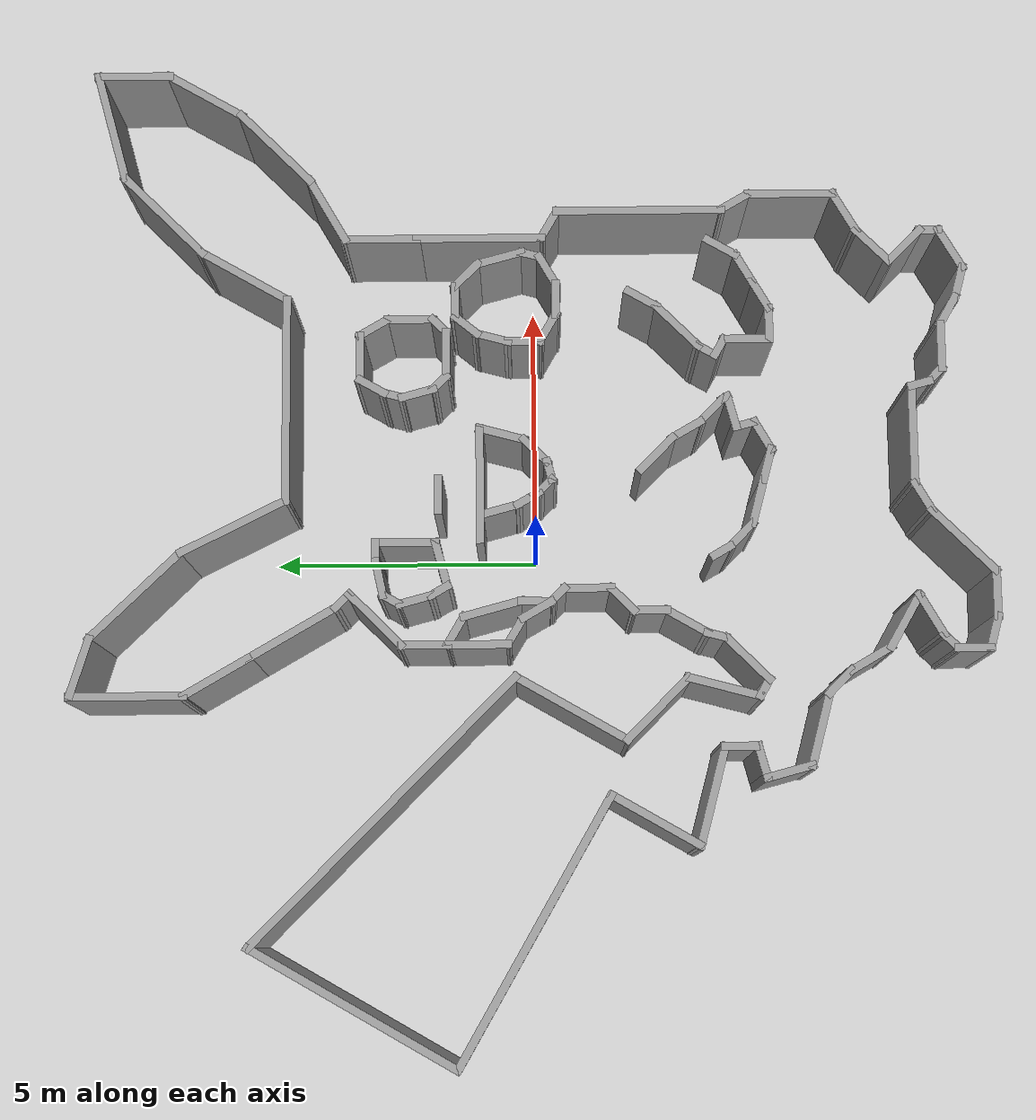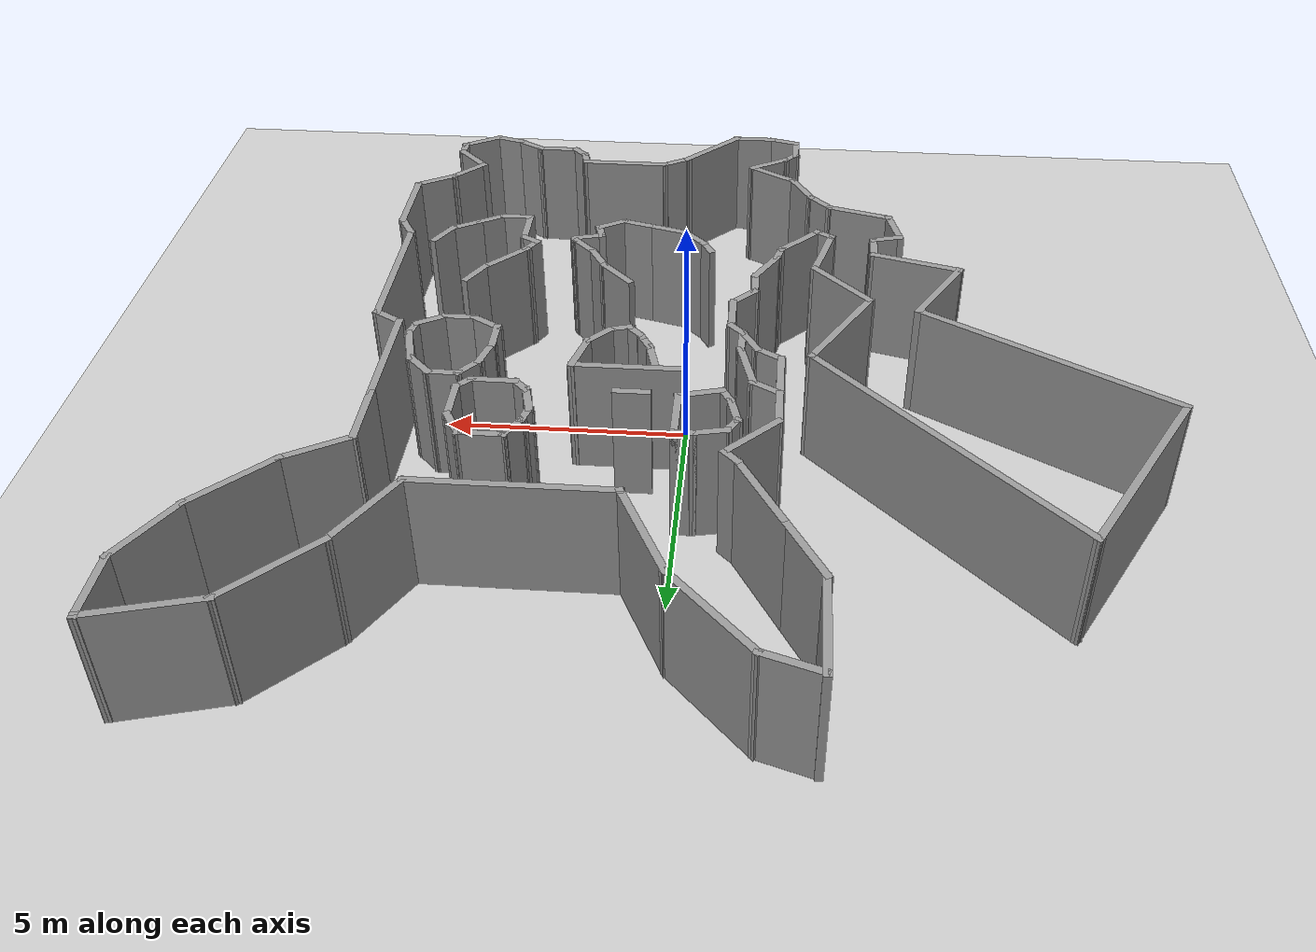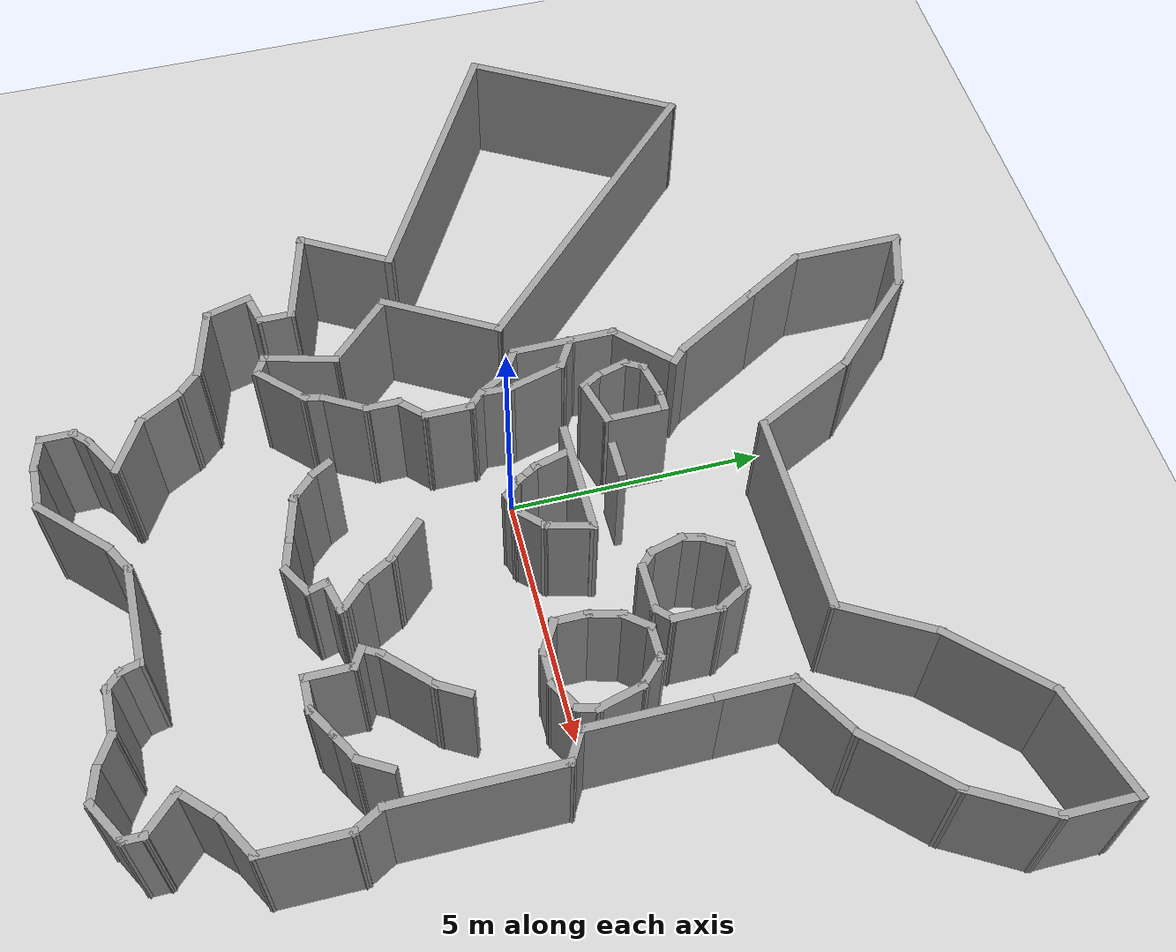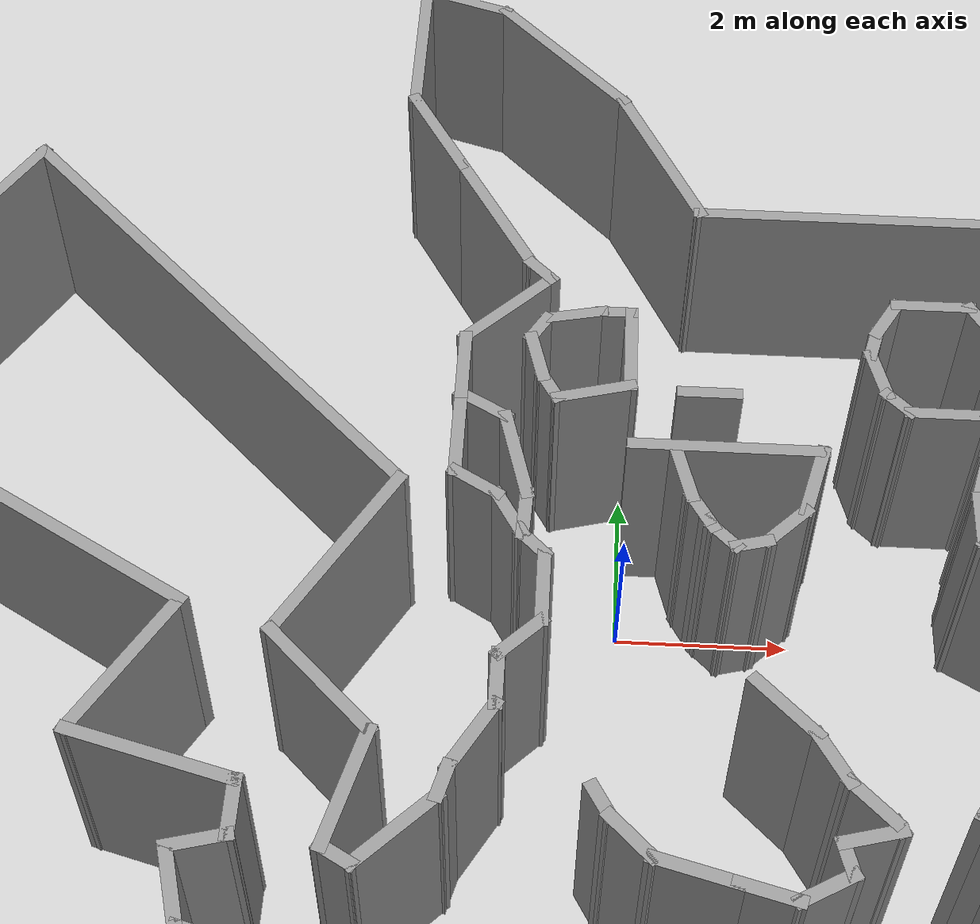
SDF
<sdf version="1.7">
 <world name="default">
  <light name="sun" type="directional">
   <pose>0 0 10 0 -0 0</pose>
   <diffuse>0.8 0.8 0.8 1</diffuse>
   <specular>0.2 0.2 0.2 1</specular>
   <attenuation>
    <range>1000</range>
    <constant>0.9</constant>
    <linear>0.01</linear>
    <quadratic>0.001</quadratic>
   </attenuation>
   <direction>-0.5 0.1 -0.9</direction>
   <spot><inner_angle>0</inner_angle><outer_angle>0</outer_angle><falloff>0</falloff></spot>
  </light>
  <model name="ground_plane">
   <static>1</static>
   <link name="link">
    <collision name="collision">
     <geometry><plane><normal>0 0 1</normal><size>100 100</size></plane></geometry>
     <surface>
      <contact><collide_bitmask>65535</collide_bitmask></contact>
      <friction><ode><mu>100</mu><mu2>50</mu2></ode></friction>
     </surface>
    </collision>
    <visual name="visual">
     <cast_shadows>0</cast_shadows>
     <geometry><plane><normal>0 0 1</normal><size>100 100</size></plane></geometry>
     <material>
      <script><uri>file://media/materials/scripts/gazebo.material</uri><name>Gazebo/Grey</name></script>
     </material>
    </visual>
   </link>
  </model>
  <gravity>0 0 -9.8</gravity>
  <magnetic_field>6e-06 2.3e-05 -4.2e-05</magnetic_field>
  <atmosphere type="adiabatic"/>
  <physics type="ode">
   <max_step_size>0.001</max_step_size>
   <real_time_factor>1</real_time_factor>
   <real_time_update_rate>1000</real_time_update_rate>
  </physics>
  <scene><ambient>0.4 0.4 0.4 1</ambient><background>0.7 0.7 0.7 1</background><shadows>1</shadows></scene>
  <spherical_coordinates>
   <surface_model>EARTH_WGS84</surface_model>
   <latitude_deg>0</latitude_deg>
   <longitude_deg>0</longitude_deg>
   <elevation>0</elevation>
   <heading_deg>0</heading_deg>
  </spherical_coordinates>
  <model name="pikachu">
   <pose>-0.20309 0.029445 0 0 -0 0</pose>
   <link name="Wall_150">
    <collision name="Wall_150_Collision">
     <geometry><box><size>1.24128 0.15 2.5</size></box></geometry>
     <pose>0 0 1.25 0 -0 0</pose>
    </collision>
    <visual name="Wall_150_Visual">
     <pose>0 0 1.25 0 -0 0</pose>
     <geometry><box><size>1.24128 0.15 2.5</size></box></geometry>
     <material>
      <script><uri>file://media/materials/scripts/gazebo.material</uri><name>Gazebo/Grey</name></script>
      <ambient>1 1 1 1</ambient>
     </material>
     <meta><layer>0</layer></meta>
    </visual>
    <pose>-2.03907 8.34284 0 0 -0 -0.306851</pose>
   </link>
   <link name="Wall_151">
    <collision name="Wall_151_Collision">
     <geometry><box><size>2.4345 0.15 2.5</size></box></geometry>
     <pose>0 0 1.25 0 -0 0</pose>
    </collision>
    <visual name="Wall_151_Visual">
     <pose>0 0 1.25 0 -0 0</pose>
     <geometry><box><size>2.4345 0.15 2.5</size></box></geometry>
     <material>
      <script><uri>file://media/materials/scripts/gazebo.material</uri><name>Gazebo/Grey</name></script>
      <ambient>1 1 1 1</ambient>
     </material>
     <meta><layer>0</layer></meta>
    </visual>
    <pose>-0.729636 7.3595 0 0 -0 -0.808021</pose>
   </link>
   <link name="Wall_152">
    <collision name="Wall_152_Collision">
     <geometry><box><size>2.29967 0.15 2.5</size></box></geometry>
     <pose>0 0 1.25 0 -0 0</pose>
    </collision>
    <visual name="Wall_152_Visual">
     <pose>0 0 1.25 0 -0 0</pose>
     <geometry><box><size>2.29967 0.15 2.5</size></box></geometry>
     <material>
      <script><uri>file://media/materials/scripts/gazebo.material</uri><name>Gazebo/Grey</name></script>
      <ambient>1 1 1 1</ambient>
     </material>
     <meta><layer>0</layer></meta>
    </visual>
    <pose>0.544827 5.5636 0 0 -0 -1.11007</pose>
   </link>
   <link name="Wall_153">
    <collision name="Wall_153_Collision">
     <geometry><box><size>4 0.15 2.5</size></box></geometry>
     <pose>0 0 1.25 0 -0 0</pose>
    </collision>
    <visual name="Wall_153_Visual">
     <pose>0 0 1.25 0 -0 0</pose>
     <geometry><box><size>4 0.15 2.5</size></box></geometry>
     <material>
      <script><uri>file://media/materials/scripts/gazebo.material</uri><name>Gazebo/Grey</name></script>
      <ambient>1 1 1 1</ambient>
     </material>
     <meta><layer>0</layer></meta>
    </visual>
    <pose>2.94769 4.60083 0 0 -0 0</pose>
   </link>
   <link name="Wall_154">
    <collision name="Wall_154_Collision">
     <geometry><box><size>2 0.15 2.5</size></box></geometry>
     <pose>0 0 1.25 0 -0 0</pose>
    </collision>
    <visual name="Wall_154_Visual">
     <pose>0 0 1.25 0 -0 0</pose>
     <geometry><box><size>2 0.15 2.5</size></box></geometry>
     <material>
      <script><uri>file://media/materials/scripts/gazebo.material</uri><name>Gazebo/Grey</name></script>
      <ambient>1 1 1 1</ambient>
     </material>
     <meta><layer>0</layer></meta>
    </visual>
    <pose>5.33519 5.40191 0 0 -0 1.0472</pose>
   </link>
   <link name="Wall_155">
    <collision name="Wall_155_Collision">
     <geometry><box><size>2.25 0.15 2.5</size></box></geometry>
     <pose>0 0 1.25 0 -0 0</pose>
    </collision>
    <visual name="Wall_155_Visual">
     <pose>0 0 1.25 0 -0 0</pose>
     <geometry><box><size>2.25 0.15 2.5</size></box></geometry>
     <material>
      <script><uri>file://media/materials/scripts/gazebo.material</uri><name>Gazebo/Grey</name></script>
      <ambient>1 1 1 1</ambient>
     </material>
     <meta><layer>0</layer></meta>
    </visual>
    <pose>6.54016 6.94544 0 0 -0 0.785398</pose>
   </link>
   <link name="Wall_156">
    <collision name="Wall_156_Collision">
     <geometry><box><size>2.25 0.15 2.5</size></box></geometry>
     <pose>0 0 1.25 0 -0 0</pose>
    </collision>
    <visual name="Wall_156_Visual">
     <pose>0 0 1.25 0 -0 0</pose>
     <geometry><box><size>2.25 0.15 2.5</size></box></geometry>
     <material>
      <script><uri>file://media/materials/scripts/gazebo.material</uri><name>Gazebo/Grey</name></script>
      <ambient>1 1 1 1</ambient>
     </material>
     <meta><layer>0</layer></meta>
    </visual>
    <pose>8.29684 7.95966 0 0 -0 0.261799</pose>
   </link>
   <link name="Wall_157">
    <collision name="Wall_157_Collision">
     <geometry><box><size>1.5 0.15 2.5</size></box></geometry>
     <pose>0 0 1.25 0 -0 0</pose>
    </collision>
    <visual name="Wall_157_Visual">
     <pose>0 0 1.25 0 -0 0</pose>
     <geometry><box><size>1.5 0.15 2.5</size></box></geometry>
     <material>
      <script><uri>file://media/materials/scripts/gazebo.material</uri><name>Gazebo/Grey</name></script>
      <ambient>1 1 1 1</ambient>
     </material>
     <meta><layer>0</layer></meta>
    </visual>
    <pose>9.31106 7.55642 0 0 -0 -1.5708</pose>
   </link>
   <link name="Wall_158">
    <collision name="Wall_158_Collision">
     <geometry><box><size>1.75 0.15 2.5</size></box></geometry>
     <pose>0 0 1.25 0 -0 0</pose>
    </collision>
    <visual name="Wall_158_Visual">
     <pose>0 0 1.25 0 -0 0</pose>
     <geometry><box><size>1.75 0.15 2.5</size></box></geometry>
     <material>
      <script><uri>file://media/materials/scripts/gazebo.material</uri><name>Gazebo/Grey</name></script>
      <ambient>1 1 1 1</ambient>
     </material>
     <meta><layer>0</layer></meta>
    </visual>
    <pose>8.91106 6.1886 0 0 -0 -2.0944</pose>
   </link>
   <link name="Wall_159">
    <collision name="Wall_159_Collision">
     <geometry><box><size>2 0.15 2.5</size></box></geometry>
     <pose>0 0 1.25 0 -0 0</pose>
    </collision>
    <visual name="Wall_159_Visual">
     <pose>0 0 1.25 0 -0 0</pose>
     <geometry><box><size>2 0.15 2.5</size></box></geometry>
     <material>
      <script><uri>file://media/materials/scripts/gazebo.material</uri><name>Gazebo/Grey</name></script>
      <ambient>1 1 1 1</ambient>
     </material>
     <meta><layer>0</layer></meta>
    </visual>
    <pose>7.85699 4.84171 0 0 -0 -2.35619</pose>
   </link>
   <link name="Wall_160">
    <collision name="Wall_160_Collision">
     <geometry><box><size>1.5 0.15 2.5</size></box></geometry>
     <pose>0 0 1.25 0 -0 0</pose>
    </collision>
    <visual name="Wall_160_Visual">
     <pose>0 0 1.25 0 -0 0</pose>
     <geometry><box><size>1.5 0.15 2.5</size></box></geometry>
     <material>
      <script><uri>file://media/materials/scripts/gazebo.material</uri><name>Gazebo/Grey</name></script>
      <ambient>1 1 1 1</ambient>
     </material>
     <meta><layer>0</layer></meta>
    </visual>
    <pose>6.61835 3.85013 0 0 -0 -2.61799</pose>
   </link>
   <link name="Wall_161">
    <collision name="Wall_161_Collision">
     <geometry><box><size>1.5 0.15 2.5</size></box></geometry>
     <pose>0 0 1.25 0 -0 0</pose>
    </collision>
    <visual name="Wall_161_Visual">
     <pose>0 0 1.25 0 -0 0</pose>
     <geometry><box><size>1.5 0.15 2.5</size></box></geometry>
     <material>
      <script><uri>file://media/materials/scripts/gazebo.material</uri><name>Gazebo/Grey</name></script>
      <ambient>1 1 1 1</ambient>
     </material>
     <meta><layer>0</layer></meta>
    </visual>
    <pose>6.03378 2.83764 0 0 -0 -1.5708</pose>
   </link>
   <link name="Wall_162">
    <collision name="Wall_162_Collision">
     <geometry><box><size>2.5 0.15 2.5</size></box></geometry>
     <pose>0 0 1.25 0 -0 0</pose>
    </collision>
    <visual name="Wall_162_Visual">
     <pose>0 0 1.25 0 -0 0</pose>
     <geometry><box><size>2.5 0.15 2.5</size></box></geometry>
     <material>
      <script><uri>file://media/materials/scripts/gazebo.material</uri><name>Gazebo/Grey</name></script>
      <ambient>1 1 1 1</ambient>
     </material>
     <meta><layer>0</layer></meta>
    </visual>
    <pose>6.03378 0.987635 0 0 -0 -1.5708</pose>
   </link>
   <link name="Wall_163">
    <collision name="Wall_163_Collision">
     <geometry><box><size>0.75 0.15 2.5</size></box></geometry>
     <pose>0 0 1.25 0 -0 0</pose>
    </collision>
    <visual name="Wall_163_Visual">
     <pose>0 0 1.25 0 -0 0</pose>
     <geometry><box><size>0.75 0.15 2.5</size></box></geometry>
     <material>
      <script><uri>file://media/materials/scripts/gazebo.material</uri><name>Gazebo/Grey</name></script>
      <ambient>1 1 1 1</ambient>
     </material>
     <meta><layer>0</layer></meta>
    </visual>
    <pose>6.29359 -0.337365 0 0 -0 -0.523599</pose>
   </link>
   <link name="Wall_164">
    <collision name="Wall_164_Collision">
     <geometry><box><size>3.25 0.15 2.5</size></box></geometry>
     <pose>0 0 1.25 0 -0 0</pose>
    </collision>
    <visual name="Wall_164_Visual">
     <pose>0 0 1.25 0 -0 0</pose>
     <geometry><box><size>3.25 0.15 2.5</size></box></geometry>
     <material>
      <script><uri>file://media/materials/scripts/gazebo.material</uri><name>Gazebo/Grey</name></script>
      <ambient>1 1 1 1</ambient>
     </material>
     <meta><layer>0</layer></meta>
    </visual>
    <pose>6.5534 -2.03736 0 0 -0 -1.5708</pose>
   </link>
   <link name="Wall_165">
    <collision name="Wall_165_Collision">
     <geometry><box><size>0.75 0.15 2.5</size></box></geometry>
     <pose>0 0 1.25 0 -0 0</pose>
    </collision>
    <visual name="Wall_165_Visual">
     <pose>0 0 1.25 0 -0 0</pose>
     <geometry><box><size>0.75 0.15 2.5</size></box></geometry>
     <material>
      <script><uri>file://media/materials/scripts/gazebo.material</uri><name>Gazebo/Grey</name></script>
      <ambient>1 1 1 1</ambient>
     </material>
     <meta><layer>0</layer></meta>
    </visual>
    <pose>6.7034 -3.84717 0 0 -0 -1.0472</pose>
   </link>
   <link name="Wall_166">
    <collision name="Wall_166_Collision">
     <geometry><box><size>1.75 0.15 2.5</size></box></geometry>
     <pose>0 0 1.25 0 -0 0</pose>
    </collision>
    <visual name="Wall_166_Visual">
     <pose>0 0 1.25 0 -0 0</pose>
     <geometry><box><size>1.75 0.15 2.5</size></box></geometry>
     <material>
      <script><uri>file://media/materials/scripts/gazebo.material</uri><name>Gazebo/Grey</name></script>
      <ambient>1 1 1 1</ambient>
     </material>
     <meta><layer>0</layer></meta>
    </visual>
    <pose>6.8534 -4.90698 0 0 -0 -1.5708</pose>
   </link>
   <link name="Wall_167">
    <collision name="Wall_167_Collision">
     <geometry><box><size>1 0.15 2.5</size></box></geometry>
     <pose>0 0 1.25 0 -0 0</pose>
    </collision>
    <visual name="Wall_167_Visual">
     <pose>0 0 1.25 0 -0 0</pose>
     <geometry><box><size>1 0.15 2.5</size></box></geometry>
     <material>
      <script><uri>file://media/materials/scripts/gazebo.material</uri><name>Gazebo/Grey</name></script>
      <ambient>1 1 1 1</ambient>
     </material>
     <meta><layer>0</layer></meta>
    </visual>
    <pose>6.48534 -5.91948 0 0 -0 -2.61799</pose>
   </link>
   <link name="Wall_168">
    <collision name="Wall_168_Collision">
     <geometry><box><size>1 0.15 2.5</size></box></geometry>
     <pose>0 0 1.25 0 -0 0</pose>
    </collision>
    <visual name="Wall_168_Visual">
     <pose>0 0 1.25 0 -0 0</pose>
     <geometry><box><size>1 0.15 2.5</size></box></geometry>
     <material>
      <script><uri>file://media/materials/scripts/gazebo.material</uri><name>Gazebo/Grey</name></script>
      <ambient>1 1 1 1</ambient>
     </material>
     <meta><layer>0</layer></meta>
    </visual>
    <pose>5.81675 -6.4325 0 0 -0 -2.35619</pose>
   </link>
   <link name="Wall_169">
    <collision name="Wall_169_Collision">
     <geometry><box><size>1 0.15 2.5</size></box></geometry>
     <pose>0 0 1.25 0 -0 0</pose>
    </collision>
    <visual name="Wall_169_Visual">
     <pose>0 0 1.25 0 -0 0</pose>
     <geometry><box><size>1 0.15 2.5</size></box></geometry>
     <material>
      <script><uri>file://media/materials/scripts/gazebo.material</uri><name>Gazebo/Grey</name></script>
      <ambient>1 1 1 1</ambient>
     </material>
     <meta><layer>0</layer></meta>
    </visual>
    <pose>5.81675 -7.03354 0 0 -0 -0.785398</pose>
   </link>
   <link name="Wall_170">
    <collision name="Wall_170_Collision">
     <geometry><box><size>0.5 0.15 2.5</size></box></geometry>
     <pose>0 0 1.25 0 -0 0</pose>
    </collision>
    <visual name="Wall_170_Visual">
     <pose>0 0 1.25 0 -0 0</pose>
     <geometry><box><size>0.5 0.15 2.5</size></box></geometry>
     <material>
      <script><uri>file://media/materials/scripts/gazebo.material</uri><name>Gazebo/Grey</name></script>
      <ambient>1 1 1 1</ambient>
     </material>
     <meta><layer>0</layer></meta>
    </visual>
    <pose>6.11728 -7.50906 0 0 -0 -1.5708</pose>
   </link>
   <link name="Wall_171">
    <collision name="Wall_171_Collision">
     <geometry><box><size>1 0.15 2.5</size></box></geometry>
     <pose>0 0 1.25 0 -0 0</pose>
    </collision>
    <visual name="Wall_171_Visual">
     <pose>0 0 1.25 0 -0 0</pose>
     <geometry><box><size>1 0.15 2.5</size></box></geometry>
     <material>
      <script><uri>file://media/materials/scripts/gazebo.material</uri><name>Gazebo/Grey</name></script>
      <ambient>1 1 1 1</ambient>
     </material>
     <meta><layer>0</layer></meta>
    </visual>
    <pose>5.74921 -7.89656 0 0 -0 -2.61799</pose>
   </link>
   <link name="Wall_172">
    <collision name="Wall_172_Collision">
     <geometry><box><size>0.75 0.15 2.5</size></box></geometry>
     <pose>0 0 1.25 0 -0 0</pose>
    </collision>
    <visual name="Wall_172_Visual">
     <pose>0 0 1.25 0 -0 0</pose>
     <geometry><box><size>0.75 0.15 2.5</size></box></geometry>
     <material>
      <script><uri>file://media/materials/scripts/gazebo.material</uri><name>Gazebo/Grey</name></script>
      <ambient>1 1 1 1</ambient>
     </material>
     <meta><layer>0</layer></meta>
    </visual>
    <pose>5.09138 -8.03142 0 0 -0 2.87979</pose>
   </link>
   <link name="Wall_173">
    <collision name="Wall_173_Collision">
     <geometry><box><size>0.75 0.15 2.5</size></box></geometry>
     <pose>0 0 1.25 0 -0 0</pose>
    </collision>
    <visual name="Wall_173_Visual">
     <pose>0 0 1.25 0 -0 0</pose>
     <geometry><box><size>0.75 0.15 2.5</size></box></geometry>
     <material>
      <script><uri>file://media/materials/scripts/gazebo.material</uri><name>Gazebo/Grey</name></script>
      <ambient>1 1 1 1</ambient>
     </material>
     <meta><layer>0</layer></meta>
    </visual>
    <pose>4.54179 -7.80377 0 0 -0 2.61799</pose>
   </link>
   <link name="Wall_174">
    <collision name="Wall_174_Collision">
     <geometry><box><size>1 0.15 2.5</size></box></geometry>
     <pose>0 0 1.25 0 -0 0</pose>
    </collision>
    <visual name="Wall_174_Visual">
     <pose>0 0 1.25 0 -0 0</pose>
     <geometry><box><size>1 0.15 2.5</size></box></geometry>
     <material>
      <script><uri>file://media/materials/scripts/gazebo.material</uri><name>Gazebo/Grey</name></script>
      <ambient>1 1 1 1</ambient>
     </material>
     <meta><layer>0</layer></meta>
    </visual>
    <pose>3.85698 -7.65377 0 0 -0 3.14159</pose>
   </link>
   <link name="Wall_175">
    <collision name="Wall_175_Collision">
     <geometry><box><size>0.5 0.15 2.5</size></box></geometry>
     <pose>0 0 1.25 0 -0 0</pose>
    </collision>
    <visual name="Wall_175_Visual">
     <pose>0 0 1.25 0 -0 0</pose>
     <geometry><box><size>0.5 0.15 2.5</size></box></geometry>
     <material>
      <script><uri>file://media/materials/scripts/gazebo.material</uri><name>Gazebo/Grey</name></script>
      <ambient>1 1 1 1</ambient>
     </material>
     <meta><layer>0</layer></meta>
    </visual>
    <pose>3.30824 -7.53003 0 0 -0 2.35619</pose>
   </link>
   <link name="Wall_176">
    <collision name="Wall_176_Collision">
     <geometry><box><size>0.5 0.15 2.5</size></box></geometry>
     <pose>0 0 1.25 0 -0 0</pose>
    </collision>
    <visual name="Wall_176_Visual">
     <pose>0 0 1.25 0 -0 0</pose>
     <geometry><box><size>0.5 0.15 2.5</size></box></geometry>
     <material>
      <script><uri>file://media/materials/scripts/gazebo.material</uri><name>Gazebo/Grey</name></script>
      <ambient>1 1 1 1</ambient>
     </material>
     <meta><layer>0</layer></meta>
    </visual>
    <pose>3.1392 -7.23725 0 0 -0 1.8326</pose>
   </link>
   <link name="Wall_177">
    <collision name="Wall_177_Collision">
     <geometry><box><size>2 0.15 2.5</size></box></geometry>
     <pose>0 0 1.25 0 -0 0</pose>
    </collision>
    <visual name="Wall_177_Visual">
     <pose>0 0 1.25 0 -0 0</pose>
     <geometry><box><size>2 0.15 2.5</size></box></geometry>
     <material>
      <script><uri>file://media/materials/scripts/gazebo.material</uri><name>Gazebo/Grey</name></script>
      <ambient>1 1 1 1</ambient>
     </material>
     <meta><layer>0</layer></meta>
    </visual>
    <pose>2.16891 -7.06821 0 0 -0 3.14159</pose>
   </link>
   <link name="Wall_178">
    <collision name="Wall_178_Collision">
     <geometry><box><size>0.75 0.15 2.5</size></box></geometry>
     <pose>0 0 1.25 0 -0 0</pose>
    </collision>
    <visual name="Wall_178_Visual">
     <pose>0 0 1.25 0 -0 0</pose>
     <geometry><box><size>0.75 0.15 2.5</size></box></geometry>
     <material>
      <script><uri>file://media/materials/scripts/gazebo.material</uri><name>Gazebo/Grey</name></script>
      <ambient>1 1 1 1</ambient>
     </material>
     <meta><layer>0</layer></meta>
    </visual>
    <pose>0.984101 -7.21821 0 0 -0 -2.61799</pose>
   </link>
   <link name="Wall_179">
    <collision name="Wall_179_Collision">
     <geometry><box><size>1.75 0.15 2.5</size></box></geometry>
     <pose>0 0 1.25 0 -0 0</pose>
    </collision>
    <visual name="Wall_179_Visual">
     <pose>0 0 1.25 0 -0 0</pose>
     <geometry><box><size>1.75 0.15 2.5</size></box></geometry>
     <material>
      <script><uri>file://media/materials/scripts/gazebo.material</uri><name>Gazebo/Grey</name></script>
      <ambient>1 1 1 1</ambient>
     </material>
     <meta><layer>0</layer></meta>
    </visual>
    <pose>0.158608 -7.93389 0 0 -0 -2.35619</pose>
   </link>
   <link name="Wall_180">
    <collision name="Wall_180_Collision">
     <geometry><box><size>1 0.15 2.5</size></box></geometry>
     <pose>0 0 1.25 0 -0 0</pose>
    </collision>
    <visual name="Wall_180_Visual">
     <pose>0 0 1.25 0 -0 0</pose>
     <geometry><box><size>1 0.15 2.5</size></box></geometry>
     <material>
      <script><uri>file://media/materials/scripts/gazebo.material</uri><name>Gazebo/Grey</name></script>
      <ambient>1 1 1 1</ambient>
     </material>
     <meta><layer>0</layer></meta>
    </visual>
    <pose>-0.832078 -8.49958 0 0 -0 3.14159</pose>
   </link>
   <link name="Wall_181">
    <collision name="Wall_181_Collision">
     <geometry><box><size>0.75 0.15 2.5</size></box></geometry>
     <pose>0 0 1.25 0 -0 0</pose>
    </collision>
    <visual name="Wall_181_Visual">
     <pose>0 0 1.25 0 -0 0</pose>
     <geometry><box><size>0.75 0.15 2.5</size></box></geometry>
     <material>
      <script><uri>file://media/materials/scripts/gazebo.material</uri><name>Gazebo/Grey</name></script>
      <ambient>1 1 1 1</ambient>
     </material>
     <meta><layer>0</layer></meta>
    </visual>
    <pose>-1.54686 -8.42193 0 0 -0 2.87979</pose>
   </link>
   <link name="Wall_182">
    <collision name="Wall_182_Collision">
     <geometry><box><size>0.75 0.15 2.5</size></box></geometry>
     <pose>0 0 1.25 0 -0 0</pose>
    </collision>
    <visual name="Wall_182_Visual">
     <pose>0 0 1.25 0 -0 0</pose>
     <geometry><box><size>0.75 0.15 2.5</size></box></geometry>
     <material>
      <script><uri>file://media/materials/scripts/gazebo.material</uri><name>Gazebo/Grey</name></script>
      <ambient>1 1 1 1</ambient>
     </material>
     <meta><layer>0</layer></meta>
    </visual>
    <pose>-1.83663 -8.04429 0 0 -0 1.5708</pose>
   </link>
   <link name="Wall_183">
    <collision name="Wall_183_Collision">
     <geometry><box><size>0.5 0.15 2.5</size></box></geometry>
     <pose>0 0 1.25 0 -0 0</pose>
    </collision>
    <visual name="Wall_183_Visual">
     <pose>0 0 1.25 0 -0 0</pose>
     <geometry><box><size>0.5 0.15 2.5</size></box></geometry>
     <material>
      <script><uri>file://media/materials/scripts/gazebo.material</uri><name>Gazebo/Grey</name></script>
      <ambient>1 1 1 1</ambient>
     </material>
     <meta><layer>0</layer></meta>
    </visual>
    <pose>-1.71289 -7.62054 0 0 -0 0.785398</pose>
   </link>
   <link name="Wall_184">
    <collision name="Wall_184_Collision">
     <geometry><box><size>1 0.15 2.5</size></box></geometry>
     <pose>0 0 1.25 0 -0 0</pose>
    </collision>
    <visual name="Wall_184_Visual">
     <pose>0 0 1.25 0 -0 0</pose>
     <geometry><box><size>1 0.15 2.5</size></box></geometry>
     <material>
      <script><uri>file://media/materials/scripts/gazebo.material</uri><name>Gazebo/Grey</name></script>
      <ambient>1 1 1 1</ambient>
     </material>
     <meta><layer>0</layer></meta>
    </visual>
    <pose>-1.22108 -7.2843 0 0 -0 0.523599</pose>
   </link>
   <link name="Wall_185">
    <collision name="Wall_185_Collision">
     <geometry><box><size>1.25 0.15 2.5</size></box></geometry>
     <pose>0 0 1.25 0 -0 0</pose>
    </collision>
    <visual name="Wall_185_Visual">
     <pose>0 0 1.25 0 -0 0</pose>
     <geometry><box><size>1.25 0.15 2.5</size></box></geometry>
     <material>
      <script><uri>file://media/materials/scripts/gazebo.material</uri><name>Gazebo/Grey</name></script>
      <ambient>1 1 1 1</ambient>
     </material>
     <meta><layer>0</layer></meta>
    </visual>
    <pose>-1.32934 -6.7968 0 0 -0 2.61799</pose>
   </link>
   <link name="Wall_186">
    <collision name="Wall_186_Collision">
     <geometry><box><size>1 0.15 2.5</size></box></geometry>
     <pose>0 0 1.25 0 -0 0</pose>
    </collision>
    <visual name="Wall_186_Visual">
     <pose>0 0 1.25 0 -0 0</pose>
     <geometry><box><size>1 0.15 2.5</size></box></geometry>
     <material>
      <script><uri>file://media/materials/scripts/gazebo.material</uri><name>Gazebo/Grey</name></script>
      <ambient>1 1 1 1</ambient>
     </material>
     <meta><layer>0</layer></meta>
    </visual>
    <pose>-2.01815 -6.15374 0 0 -0 2.0944</pose>
   </link>
   <link name="Wall_187">
    <collision name="Wall_187_Collision">
     <geometry><box><size>0.75 0.15 2.5</size></box></geometry>
     <pose>0 0 1.25 0 -0 0</pose>
    </collision>
    <visual name="Wall_187_Visual">
     <pose>0 0 1.25 0 -0 0</pose>
     <geometry><box><size>0.75 0.15 2.5</size></box></geometry>
     <material>
      <script><uri>file://media/materials/scripts/gazebo.material</uri><name>Gazebo/Grey</name></script>
      <ambient>1 1 1 1</ambient>
     </material>
     <meta><layer>0</layer></meta>
    </visual>
    <pose>-2.44278 -5.57355 0 0 -0 2.35619</pose>
   </link>
   <link name="Wall_188">
    <collision name="Wall_188_Collision">
     <geometry><box><size>1.5 0.15 2.5</size></box></geometry>
     <pose>0 0 1.25 0 -0 0</pose>
    </collision>
    <visual name="Wall_188_Visual">
     <pose>0 0 1.25 0 -0 0</pose>
     <geometry><box><size>1.5 0.15 2.5</size></box></geometry>
     <material>
      <script><uri>file://media/materials/scripts/gazebo.material</uri><name>Gazebo/Grey</name></script>
      <ambient>1 1 1 1</ambient>
     </material>
     <meta><layer>0</layer></meta>
    </visual>
    <pose>-3.30692 -5.18671 0 0 -0 2.87979</pose>
   </link>
   <link name="Wall_189">
    <collision name="Wall_189_Collision">
     <geometry><box><size>1 0.15 2.5</size></box></geometry>
     <pose>0 0 1.25 0 -0 0</pose>
    </collision>
    <visual name="Wall_189_Visual">
     <pose>0 0 1.25 0 -0 0</pose>
     <geometry><box><size>1 0.15 2.5</size></box></geometry>
     <material>
      <script><uri>file://media/materials/scripts/gazebo.material</uri><name>Gazebo/Grey</name></script>
      <ambient>1 1 1 1</ambient>
     </material>
     <meta><layer>0</layer></meta>
    </visual>
    <pose>-4.06891 -4.60149 0 0 -0 1.8326</pose>
   </link>
   <link name="Wall_190">
    <collision name="Wall_190_Collision">
     <geometry><box><size>0.75 0.15 2.5</size></box></geometry>
     <pose>0 0 1.25 0 -0 0</pose>
    </collision>
    <visual name="Wall_190_Visual">
     <pose>0 0 1.25 0 -0 0</pose>
     <geometry><box><size>0.75 0.15 2.5</size></box></geometry>
     <material>
      <script><uri>file://media/materials/scripts/gazebo.material</uri><name>Gazebo/Grey</name></script>
      <ambient>1 1 1 1</ambient>
     </material>
     <meta><layer>0</layer></meta>
    </visual>
    <pose>-3.88913 -4.11333 0 0 -0 0.261799</pose>
   </link>
   <link name="Wall_191">
    <collision name="Wall_191_Collision">
     <geometry><box><size>0.75 0.15 2.5</size></box></geometry>
     <pose>0 0 1.25 0 -0 0</pose>
    </collision>
    <visual name="Wall_191_Visual">
     <pose>0 0 1.25 0 -0 0</pose>
     <geometry><box><size>0.75 0.15 2.5</size></box></geometry>
     <material>
      <script><uri>file://media/materials/scripts/gazebo.material</uri><name>Gazebo/Grey</name></script>
      <ambient>1 1 1 1</ambient>
     </material>
     <meta><layer>0</layer></meta>
    </visual>
    <pose>-3.59936 -3.73568 0 0 -0 1.5708</pose>
   </link>
   <link name="Wall_192">
    <collision name="Wall_192_Collision">
     <geometry><box><size>2 0.15 2.5</size></box></geometry>
     <pose>0 0 1.25 0 -0 0</pose>
    </collision>
    <visual name="Wall_192_Visual">
     <pose>0 0 1.25 0 -0 0</pose>
     <geometry><box><size>2 0.15 2.5</size></box></geometry>
     <material>
      <script><uri>file://media/materials/scripts/gazebo.material</uri><name>Gazebo/Grey</name></script>
      <ambient>1 1 1 1</ambient>
     </material>
     <meta><layer>0</layer></meta>
    </visual>
    <pose>-4.49284 -3.19627 0 0 -0 2.87979</pose>
   </link>
   <link name="Wall_193">
    <collision name="Wall_193_Collision">
     <geometry><box><size>2 0.15 2.5</size></box></geometry>
     <pose>0 0 1.25 0 -0 0</pose>
    </collision>
    <visual name="Wall_193_Visual">
     <pose>0 0 1.25 0 -0 0</pose>
     <geometry><box><size>2 0.15 2.5</size></box></geometry>
     <material>
      <script><uri>file://media/materials/scripts/gazebo.material</uri><name>Gazebo/Grey</name></script>
      <ambient>1 1 1 1</ambient>
     </material>
     <meta><layer>0</layer></meta>
    </visual>
    <pose>-4.92382 -2.15579 0 0 -0 1.0472</pose>
   </link>
   <link name="Wall_194">
    <collision name="Wall_194_Collision">
     <geometry><box><size>5.75 0.15 2.5</size></box></geometry>
     <pose>0 0 1.25 0 -0 0</pose>
    </collision>
    <visual name="Wall_194_Visual">
     <pose>0 0 1.25 0 -0 0</pose>
     <geometry><box><size>5.75 0.15 2.5</size></box></geometry>
     <material>
      <script><uri>file://media/materials/scripts/gazebo.material</uri><name>Gazebo/Grey</name></script>
      <ambient>1 1 1 1</ambient>
     </material>
     <meta><layer>0</layer></meta>
    </visual>
    <pose>-6.88619 0.045281 0 0 -0 2.61799</pose>
   </link>
   <link name="Wall_195">
    <collision name="Wall_195_Collision">
     <geometry><box><size>4.5 0.15 2.5</size></box></geometry>
     <pose>0 0 1.25 0 -0 0</pose>
    </collision>
    <visual name="Wall_195_Visual">
     <pose>0 0 1.25 0 -0 0</pose>
     <geometry><box><size>4.5 0.15 2.5</size></box></geometry>
     <material>
      <script><uri>file://media/materials/scripts/gazebo.material</uri><name>Gazebo/Grey</name></script>
      <ambient>1 1 1 1</ambient>
     </material>
     <meta><layer>0</layer></meta>
    </visual>
    <pose>-8.22356 3.32889 0 0 -0 1.0472</pose>
   </link>
   <link name="Wall_196">
    <collision name="Wall_196_Collision">
     <geometry><box><size>7 0.15 2.5</size></box></geometry>
     <pose>0 0 1.25 0 -0 0</pose>
    </collision>
    <visual name="Wall_196_Visual">
     <pose>0 0 1.25 0 -0 0</pose>
     <geometry><box><size>7 0.15 2.5</size></box></geometry>
     <material>
      <script><uri>file://media/materials/scripts/gazebo.material</uri><name>Gazebo/Grey</name></script>
      <ambient>1 1 1 1</ambient>
     </material>
     <meta><layer>0</layer></meta>
    </visual>
    <pose>-4.71422 2.79065 0 0 -0 -0.785398</pose>
   </link>
   <link name="Wall_197">
    <collision name="Wall_197_Collision">
     <geometry><box><size>2.5 0.15 2.5</size></box></geometry>
     <pose>0 0 1.25 0 -0 0</pose>
    </collision>
    <visual name="Wall_197_Visual">
     <pose>0 0 1.25 0 -0 0</pose>
     <geometry><box><size>2.5 0.15 2.5</size></box></geometry>
     <material>
      <script><uri>file://media/materials/scripts/gazebo.material</uri><name>Gazebo/Grey</name></script>
      <ambient>1 1 1 1</ambient>
     </material>
     <meta><layer>0</layer></meta>
    </visual>
    <pose>-2.87988 -0.64877 0 0 -0 -2.0944</pose>
   </link>
   <link name="Wall_198">
    <collision name="Wall_198_Collision">
     <geometry><box><size>1.75 0.15 2.5</size></box></geometry>
     <pose>0 0 1.25 0 -0 0</pose>
    </collision>
    <visual name="Wall_198_Visual">
     <pose>0 0 1.25 0 -0 0</pose>
     <geometry><box><size>1.75 0.15 2.5</size></box></geometry>
     <material>
      <script><uri>file://media/materials/scripts/gazebo.material</uri><name>Gazebo/Grey</name></script>
      <ambient>1 1 1 1</ambient>
     </material>
     <meta><layer>0</layer></meta>
    </visual>
    <pose>-2.9017 -2.23204 0 0 -0 -0.785398</pose>
   </link>
   <link name="Wall_199">
    <collision name="Wall_199_Collision">
     <geometry><box><size>1.5 0.15 2.5</size></box></geometry>
     <pose>0 0 1.25 0 -0 0</pose>
    </collision>
    <visual name="Wall_199_Visual">
     <pose>0 0 1.25 0 -0 0</pose>
     <geometry><box><size>1.5 0.15 2.5</size></box></geometry>
     <material>
      <script><uri>file://media/materials/scripts/gazebo.material</uri><name>Gazebo/Grey</name></script>
      <ambient>1 1 1 1</ambient>
     </material>
     <meta><layer>0</layer></meta>
    </visual>
    <pose>-2.51071 -3.44972 0 0 -0 -1.8326</pose>
   </link>
   <link name="Wall_200">
    <collision name="Wall_200_Collision">
     <geometry><box><size>0.5 0.15 2.5</size></box></geometry>
     <pose>0 0 1.25 0 -0 0</pose>
    </collision>
    <visual name="Wall_200_Visual">
     <pose>0 0 1.25 0 -0 0</pose>
     <geometry><box><size>0.5 0.15 2.5</size></box></geometry>
     <material>
      <script><uri>file://media/materials/scripts/gazebo.material</uri><name>Gazebo/Grey</name></script>
      <ambient>1 1 1 1</ambient>
     </material>
     <meta><layer>0</layer></meta>
    </visual>
    <pose>-2.53386 -4.18922 0 0 -0 -0.523599</pose>
   </link>
   <link name="Wall_201">
    <collision name="Wall_201_Collision">
     <geometry><box><size>1.25 0.15 2.5</size></box></geometry>
     <pose>0 0 1.25 0 -0 0</pose>
    </collision>
    <visual name="Wall_201_Visual">
     <pose>0 0 1.25 0 -0 0</pose>
     <geometry><box><size>1.25 0.15 2.5</size></box></geometry>
     <material>
      <script><uri>file://media/materials/scripts/gazebo.material</uri><name>Gazebo/Grey</name></script>
      <ambient>1 1 1 1</ambient>
     </material>
     <meta><layer>0</layer></meta>
    </visual>
    <pose>-1.9934 -3.88781 0 0 -0 0.785398</pose>
   </link>
   <link name="Wall_202">
    <collision name="Wall_202_Collision">
     <geometry><box><size>0.5 0.15 2.5</size></box></geometry>
     <pose>0 0 1.25 0 -0 0</pose>
    </collision>
    <visual name="Wall_202_Visual">
     <pose>0 0 1.25 0 -0 0</pose>
     <geometry><box><size>0.5 0.15 2.5</size></box></geometry>
     <material>
      <script><uri>file://media/materials/scripts/gazebo.material</uri><name>Gazebo/Grey</name></script>
      <ambient>1 1 1 1</ambient>
     </material>
     <meta><layer>0</layer></meta>
    </visual>
    <pose>-1.5592 -3.32987 0 0 -0 1.309</pose>
   </link>
   <link name="Wall_203">
    <collision name="Wall_203_Collision">
     <geometry><box><size>1 0.15 2.5</size></box></geometry>
     <pose>0 0 1.25 0 -0 0</pose>
    </collision>
    <visual name="Wall_203_Visual">
     <pose>0 0 1.25 0 -0 0</pose>
     <geometry><box><size>1 0.15 2.5</size></box></geometry>
     <material>
      <script><uri>file://media/materials/scripts/gazebo.material</uri><name>Gazebo/Grey</name></script>
      <ambient>1 1 1 1</ambient>
     </material>
     <meta><layer>0</layer></meta>
    </visual>
    <pose>-1.3014 -2.79277 0 0 -0 1.0472</pose>
   </link>
   <link name="Wall_204">
    <collision name="Wall_204_Collision">
     <geometry><box><size>0.75 0.15 2.5</size></box></geometry>
     <pose>0 0 1.25 0 -0 0</pose>
    </collision>
    <visual name="Wall_204_Visual">
     <pose>0 0 1.25 0 -0 0</pose>
     <geometry><box><size>0.75 0.15 2.5</size></box></geometry>
     <material>
      <script><uri>file://media/materials/scripts/gazebo.material</uri><name>Gazebo/Grey</name></script>
      <ambient>1 1 1 1</ambient>
     </material>
     <meta><layer>0</layer></meta>
    </visual>
    <pose>-1.0889 -2.12471 0 0 -0 1.5708</pose>
   </link>
   <link name="Wall_205">
    <collision name="Wall_205_Collision">
     <geometry><box><size>0.75 0.15 2.5</size></box></geometry>
     <pose>0 0 1.25 0 -0 0</pose>
    </collision>
    <visual name="Wall_205_Visual">
     <pose>0 0 1.25 0 -0 0</pose>
     <geometry><box><size>0.75 0.15 2.5</size></box></geometry>
     <material>
      <script><uri>file://media/materials/scripts/gazebo.material</uri><name>Gazebo/Grey</name></script>
      <ambient>1 1 1 1</ambient>
     </material>
     <meta><layer>0</layer></meta>
    </visual>
    <pose>-0.87677 -1.61258 0 0 -0 0.785398</pose>
   </link>
   <link name="Wall_206">
    <collision name="Wall_206_Collision">
     <geometry><box><size>1 0.15 2.5</size></box></geometry>
     <pose>0 0 1.25 0 -0 0</pose>
    </collision>
    <visual name="Wall_206_Visual">
     <pose>0 0 1.25 0 -0 0</pose>
     <geometry><box><size>1 0.15 2.5</size></box></geometry>
     <material>
      <script><uri>file://media/materials/scripts/gazebo.material</uri><name>Gazebo/Grey</name></script>
      <ambient>1 1 1 1</ambient>
     </material>
     <meta><layer>0</layer></meta>
    </visual>
    <pose>-0.664638 -0.975443 0 0 -0 1.5708</pose>
   </link>
   <link name="Wall_207">
    <collision name="Wall_207_Collision">
     <geometry><box><size>0.5 0.15 2.5</size></box></geometry>
     <pose>0 0 1.25 0 -0 0</pose>
    </collision>
    <visual name="Wall_207_Visual">
     <pose>0 0 1.25 0 -0 0</pose>
     <geometry><box><size>0.5 0.15 2.5</size></box></geometry>
     <material>
      <script><uri>file://media/materials/scripts/gazebo.material</uri><name>Gazebo/Grey</name></script>
      <ambient>1 1 1 1</ambient>
     </material>
     <meta><layer>0</layer></meta>
    </visual>
    <pose>-0.788382 -0.426699 0 0 -0 2.35619</pose>
   </link>
   <link name="Wall_208">
    <collision name="Wall_208_Collision">
     <geometry><box><size>0.75 0.15 2.5</size></box></geometry>
     <pose>0 0 1.25 0 -0 0</pose>
    </collision>
    <visual name="Wall_208_Visual">
     <pose>0 0 1.25 0 -0 0</pose>
     <geometry><box><size>0.75 0.15 2.5</size></box></geometry>
     <material>
      <script><uri>file://media/materials/scripts/gazebo.material</uri><name>Gazebo/Grey</name></script>
      <ambient>1 1 1 1</ambient>
     </material>
     <meta><layer>0</layer></meta>
    </visual>
    <pose>-1.06212 -0.043148 0 0 -0 2.0944</pose>
   </link>
   <link name="Wall_214">
    <collision name="Wall_214_Collision">
     <geometry><box><size>2.25 0.15 2.5</size></box></geometry>
     <pose>0 0 1.25 0 -0 0</pose>
    </collision>
    <visual name="Wall_214_Visual">
     <pose>0 0 1.25 0 -0 0</pose>
     <geometry><box><size>2.25 0.15 2.5</size></box></geometry>
     <material>
      <script><uri>file://media/materials/scripts/gazebo.material</uri><name>Gazebo/Grey</name></script>
      <ambient>1 1 1 1</ambient>
     </material>
     <meta><layer>0</layer></meta>
    </visual>
    <pose>-2.58621 7.48065 0 0 -0 -1.5708</pose>
   </link>
   <link name="Wall_215">
    <collision name="Wall_215_Collision">
     <geometry><box><size>1.5 0.15 2.5</size></box></geometry>
     <pose>0 0 1.25 0 -0 0</pose>
    </collision>
    <visual name="Wall_215_Visual">
     <pose>0 0 1.25 0 -0 0</pose>
     <geometry><box><size>1.5 0.15 2.5</size></box></geometry>
     <material>
      <script><uri>file://media/materials/scripts/gazebo.material</uri><name>Gazebo/Grey</name></script>
      <ambient>1 1 1 1</ambient>
     </material>
     <meta><layer>0</layer></meta>
    </visual>
    <pose>-2.24871 5.84608 0 0 -0 -1.0472</pose>
   </link>
   <link name="Wall_216">
    <collision name="Wall_216_Collision">
     <geometry><box><size>2 0.15 2.5</size></box></geometry>
     <pose>0 0 1.25 0 -0 0</pose>
    </collision>
    <visual name="Wall_216_Visual">
     <pose>0 0 1.25 0 -0 0</pose>
     <geometry><box><size>2 0.15 2.5</size></box></geometry>
     <material>
      <script><uri>file://media/materials/scripts/gazebo.material</uri><name>Gazebo/Grey</name></script>
      <ambient>1 1 1 1</ambient>
     </material>
     <meta><layer>0</layer></meta>
    </visual>
    <pose>-1.44871 4.46044 0 0 -0 -1.0472</pose>
   </link>
   <link name="Wall_217">
    <collision name="Wall_217_Collision">
     <geometry><box><size>0.5 0.15 2.5</size></box></geometry>
     <pose>0 0 1.25 0 -0 0</pose>
    </collision>
    <visual name="Wall_217_Visual">
     <pose>0 0 1.25 0 -0 0</pose>
     <geometry><box><size>0.5 0.15 2.5</size></box></geometry>
     <material>
      <script><uri>file://media/materials/scripts/gazebo.material</uri><name>Gazebo/Grey</name></script>
      <ambient>1 1 1 1</ambient>
     </material>
     <meta><layer>0</layer></meta>
    </visual>
    <pose>-0.862463 3.53562 0 0 -0 -0.785398</pose>
   </link>
   <link name="Wall_218">
    <collision name="Wall_218_Collision">
     <geometry><box><size>1.5 0.15 2.5</size></box></geometry>
     <pose>0 0 1.25 0 -0 0</pose>
    </collision>
    <visual name="Wall_218_Visual">
     <pose>0 0 1.25 0 -0 0</pose>
     <geometry><box><size>1.5 0.15 2.5</size></box></geometry>
     <material>
      <script><uri>file://media/materials/scripts/gazebo.material</uri><name>Gazebo/Grey</name></script>
      <ambient>1 1 1 1</ambient>
     </material>
     <meta><layer>0</layer></meta>
    </visual>
    <pose>-1.21602 2.93458 0 0 -0 -2.35619</pose>
   </link>
   <link name="Wall_219">
    <collision name="Wall_219_Collision">
     <geometry><box><size>1 0.15 2.5</size></box></geometry>
     <pose>0 0 1.25 0 -0 0</pose>
    </collision>
    <visual name="Wall_219_Visual">
     <pose>0 0 1.25 0 -0 0</pose>
     <geometry><box><size>1 0.15 2.5</size></box></geometry>
     <material>
      <script><uri>file://media/materials/scripts/gazebo.material</uri><name>Gazebo/Grey</name></script>
      <ambient>1 1 1 1</ambient>
     </material>
     <meta><layer>0</layer></meta>
    </visual>
    <pose>-1.69331 2.03228 0 0 -0 -1.5708</pose>
   </link>
   <link name="Wall_220">
    <collision name="Wall_220_Collision">
     <geometry><box><size>1.25 0.15 2.5</size></box></geometry>
     <pose>0 0 1.25 0 -0 0</pose>
    </collision>
    <visual name="Wall_220_Visual">
     <pose>0 0 1.25 0 -0 0</pose>
     <geometry><box><size>1.25 0.15 2.5</size></box></geometry>
     <material>
      <script><uri>file://media/materials/scripts/gazebo.material</uri><name>Gazebo/Grey</name></script>
      <ambient>1 1 1 1</ambient>
     </material>
     <meta><layer>0</layer></meta>
    </visual>
    <pose>-1.69331 1.05728 0 0 -0 -1.5708</pose>
   </link>
   <link name="Wall_221">
    <collision name="Wall_221_Collision">
     <geometry><box><size>0.712143 0.15 2.5</size></box></geometry>
     <pose>0 0 1.25 0 -0 0</pose>
    </collision>
    <visual name="Wall_221_Visual">
     <pose>0 0 1.25 0 -0 0</pose>
     <geometry><box><size>0.712143 0.15 2.5</size></box></geometry>
     <material>
      <script><uri>file://media/materials/scripts/gazebo.material</uri><name>Gazebo/Grey</name></script>
      <ambient>1 1 1 1</ambient>
     </material>
     <meta><layer>0</layer></meta>
    </visual>
    <pose>-1.45272 0.361971 0 0 -0 -0.543334</pose>
   </link>
   <link name="Wall_231">
    <collision name="Wall_231_Collision">
     <geometry><box><size>0.15 0.15 2.5</size></box></geometry>
     <pose>0 0 1.25 0 -0 0</pose>
    </collision>
    <visual name="Wall_231_Visual">
     <pose>0 0 1.25 0 -0 0</pose>
     <geometry><box><size>0.15 0.15 2.5</size></box></geometry>
     <material>
      <script><uri>file://media/materials/scripts/gazebo.material</uri><name>Gazebo/Grey</name></script>
      <ambient>1 1 1 1</ambient>
     </material>
     <meta><layer>0</layer></meta>
    </visual>
    <pose>-0.133514 2.92781 0 0 -0 0</pose>
   </link>
   <link name="Wall_233">
    <collision name="Wall_233_Collision">
     <geometry><box><size>1 0.15 2.5</size></box></geometry>
     <pose>0 0 1.25 0 -0 0</pose>
    </collision>
    <visual name="Wall_233_Visual">
     <pose>0 0 1.25 0 -0 0</pose>
     <geometry><box><size>1 0.15 2.5</size></box></geometry>
     <material>
      <script><uri>file://media/materials/scripts/gazebo.material</uri><name>Gazebo/Grey</name></script>
      <ambient>1 1 1 1</ambient>
     </material>
     <meta><layer>0</layer></meta>
    </visual>
    <pose>1.84972 -2.29317 0 0 -0 -0.785398</pose>
   </link>
   <link name="Wall_234">
    <collision name="Wall_234_Collision">
     <geometry><box><size>0.75 0.15 2.5</size></box></geometry>
     <pose>0 0 1.25 0 -0 0</pose>
    </collision>
    <visual name="Wall_234_Visual">
     <pose>0 0 1.25 0 -0 0</pose>
     <geometry><box><size>0.75 0.15 2.5</size></box></geometry>
     <material>
      <script><uri>file://media/materials/scripts/gazebo.material</uri><name>Gazebo/Grey</name></script>
      <ambient>1 1 1 1</ambient>
     </material>
     <meta><layer>0</layer></meta>
    </visual>
    <pose>2.30024 -2.8535 0 0 -0 -1.0472</pose>
   </link>
   <link name="Wall_235">
    <collision name="Wall_235_Collision">
     <geometry><box><size>0.75 0.15 2.5</size></box></geometry>
     <pose>0 0 1.25 0 -0 0</pose>
    </collision>
    <visual name="Wall_235_Visual">
     <pose>0 0 1.25 0 -0 0</pose>
     <geometry><box><size>0.75 0.15 2.5</size></box></geometry>
     <material>
      <script><uri>file://media/materials/scripts/gazebo.material</uri><name>Gazebo/Grey</name></script>
      <ambient>1 1 1 1</ambient>
     </material>
     <meta><layer>0</layer></meta>
    </visual>
    <pose>2.66237 -3.32544 0 0 -0 -0.785398</pose>
   </link>
   <link name="Wall_236">
    <collision name="Wall_236_Collision">
     <geometry><box><size>0.25 0.15 2.5</size></box></geometry>
     <pose>0 0 1.25 0 -0 0</pose>
    </collision>
    <visual name="Wall_236_Visual">
     <pose>0 0 1.25 0 -0 0</pose>
     <geometry><box><size>0.25 0.15 2.5</size></box></geometry>
     <material>
      <script><uri>file://media/materials/scripts/gazebo.material</uri><name>Gazebo/Grey</name></script>
      <ambient>1 1 1 1</ambient>
     </material>
     <meta><layer>0</layer></meta>
    </visual>
    <pose>2.89951 -3.58087 0 0 -0 -1.0472</pose>
   </link>
   <link name="Wall_237">
    <collision name="Wall_237_Collision">
     <geometry><box><size>0.75 0.15 2.5</size></box></geometry>
     <pose>0 0 1.25 0 -0 0</pose>
    </collision>
    <visual name="Wall_237_Visual">
     <pose>0 0 1.25 0 -0 0</pose>
     <geometry><box><size>0.75 0.15 2.5</size></box></geometry>
     <material>
      <script><uri>file://media/materials/scripts/gazebo.material</uri><name>Gazebo/Grey</name></script>
      <ambient>1 1 1 1</ambient>
     </material>
     <meta><layer>0</layer></meta>
    </visual>
    <pose>2.63473 -3.70182 0 0 -0 -2.87979</pose>
   </link>
   <link name="Wall_238">
    <collision name="Wall_238_Collision">
     <geometry><box><size>0.5 0.15 2.5</size></box></geometry>
     <pose>0 0 1.25 0 -0 0</pose>
    </collision>
    <visual name="Wall_238_Visual">
     <pose>0 0 1.25 0 -0 0</pose>
     <geometry><box><size>0.5 0.15 2.5</size></box></geometry>
     <material>
      <script><uri>file://media/materials/scripts/gazebo.material</uri><name>Gazebo/Grey</name></script>
      <ambient>1 1 1 1</ambient>
     </material>
     <meta><layer>0</layer></meta>
    </visual>
    <pose>2.39024 -3.9485 0 0 -0 -1.309</pose>
   </link>
   <link name="Wall_239">
    <collision name="Wall_239_Collision">
     <geometry><box><size>0.75 0.15 2.5</size></box></geometry>
     <pose>0 0 1.25 0 -0 0</pose>
    </collision>
    <visual name="Wall_239_Visual">
     <pose>0 0 1.25 0 -0 0</pose>
     <geometry><box><size>0.75 0.15 2.5</size></box></geometry>
     <material>
      <script><uri>file://media/materials/scripts/gazebo.material</uri><name>Gazebo/Grey</name></script>
      <ambient>1 1 1 1</ambient>
     </material>
     <meta><layer>0</layer></meta>
    </visual>
    <pose>2.17573 -4.26754 0 0 -0 -2.61799</pose>
   </link>
   <link name="Wall_240">
    <collision name="Wall_240_Collision">
     <geometry><box><size>0.75 0.15 2.5</size></box></geometry>
     <pose>0 0 1.25 0 -0 0</pose>
    </collision>
    <visual name="Wall_240_Visual">
     <pose>0 0 1.25 0 -0 0</pose>
     <geometry><box><size>0.75 0.15 2.5</size></box></geometry>
     <material>
      <script><uri>file://media/materials/scripts/gazebo.material</uri><name>Gazebo/Grey</name></script>
      <ambient>1 1 1 1</ambient>
     </material>
     <meta><layer>0</layer></meta>
    </visual>
    <pose>1.62614 -4.33989 0 0 -0 2.87979</pose>
   </link>
   <link name="Wall_241">
    <collision name="Wall_241_Collision">
     <geometry><box><size>1 0.15 2.5</size></box></geometry>
     <pose>0 0 1.25 0 -0 0</pose>
    </collision>
    <visual name="Wall_241_Visual">
     <pose>0 0 1.25 0 -0 0</pose>
     <geometry><box><size>1 0.15 2.5</size></box></geometry>
     <material>
      <script><uri>file://media/materials/scripts/gazebo.material</uri><name>Gazebo/Grey</name></script>
      <ambient>1 1 1 1</ambient>
     </material>
     <meta><layer>0</layer></meta>
    </visual>
    <pose>0.925849 -4.15225 0 0 -0 2.87979</pose>
   </link>
   <link name="Wall_242">
    <collision name="Wall_242_Collision">
     <geometry><box><size>0.75 0.15 2.5</size></box></geometry>
     <pose>0 0 1.25 0 -0 0</pose>
    </collision>
    <visual name="Wall_242_Visual">
     <pose>0 0 1.25 0 -0 0</pose>
     <geometry><box><size>0.75 0.15 2.5</size></box></geometry>
     <material>
      <script><uri>file://media/materials/scripts/gazebo.material</uri><name>Gazebo/Grey</name></script>
      <ambient>1 1 1 1</ambient>
     </material>
     <meta><layer>0</layer></meta>
    </visual>
    <pose>0.303198 -3.83012 0 0 -0 2.35619</pose>
   </link>
   <link name="Wall_243">
    <collision name="Wall_243_Collision">
     <geometry><box><size>0.5 0.15 2.5</size></box></geometry>
     <pose>0 0 1.25 0 -0 0</pose>
    </collision>
    <visual name="Wall_243_Visual">
     <pose>0 0 1.25 0 -0 0</pose>
     <geometry><box><size>0.5 0.15 2.5</size></box></geometry>
     <material>
      <script><uri>file://media/materials/scripts/gazebo.material</uri><name>Gazebo/Grey</name></script>
      <ambient>1 1 1 1</ambient>
     </material>
     <meta><layer>0</layer></meta>
    </visual>
    <pose>0.003566 -3.46643 0 0 -0 2.0944</pose>
   </link>
   <link name="Wall_245">
    <collision name="Wall_245_Collision">
     <geometry><box><size>0.75 0.15 2.5</size></box></geometry>
     <pose>0 0 1.25 0 -0 0</pose>
    </collision>
    <visual name="Wall_245_Visual">
     <pose>0 0 1.25 0 -0 0</pose>
     <geometry><box><size>0.75 0.15 2.5</size></box></geometry>
     <material>
      <script><uri>file://media/materials/scripts/gazebo.material</uri><name>Gazebo/Grey</name></script>
      <ambient>1 1 1 1</ambient>
     </material>
     <meta><layer>0</layer></meta>
    </visual>
    <pose>4.82883 -2.07365 0 0 -0 -2.0944</pose>
   </link>
   <link name="Wall_246">
    <collision name="Wall_246_Collision">
     <geometry><box><size>1.25 0.15 2.5</size></box></geometry>
     <pose>0 0 1.25 0 -0 0</pose>
    </collision>
    <visual name="Wall_246_Visual">
     <pose>0 0 1.25 0 -0 0</pose>
     <geometry><box><size>1.25 0.15 2.5</size></box></geometry>
     <material>
      <script><uri>file://media/materials/scripts/gazebo.material</uri><name>Gazebo/Grey</name></script>
      <ambient>1 1 1 1</ambient>
     </material>
     <meta><layer>0</layer></meta>
    </visual>
    <pose>4.28992 -2.72237 0 0 -0 -2.35619</pose>
   </link>
   <link name="Wall_247">
    <collision name="Wall_247_Collision">
     <geometry><box><size>0.5 0.15 2.5</size></box></geometry>
     <pose>0 0 1.25 0 -0 0</pose>
    </collision>
    <visual name="Wall_247_Visual">
     <pose>0 0 1.25 0 -0 0</pose>
     <geometry><box><size>0.5 0.15 2.5</size></box></geometry>
     <material>
      <script><uri>file://media/materials/scripts/gazebo.material</uri><name>Gazebo/Grey</name></script>
      <ambient>1 1 1 1</ambient>
     </material>
     <meta><layer>0</layer></meta>
    </visual>
    <pose>3.81351 -3.26283 0 0 -0 -2.0944</pose>
   </link>
   <link name="Wall_248">
    <collision name="Wall_248_Collision">
     <geometry><box><size>0.5 0.15 2.5</size></box></geometry>
     <pose>0 0 1.25 0 -0 0</pose>
    </collision>
    <visual name="Wall_248_Visual">
     <pose>0 0 1.25 0 -0 0</pose>
     <geometry><box><size>0.5 0.15 2.5</size></box></geometry>
     <material>
      <script><uri>file://media/materials/scripts/gazebo.material</uri><name>Gazebo/Grey</name></script>
      <ambient>1 1 1 1</ambient>
     </material>
     <meta><layer>0</layer></meta>
    </visual>
    <pose>3.87757 -3.50188 0 0 -0 -0.523599</pose>
   </link>
   <link name="Wall_249">
    <collision name="Wall_249_Collision">
     <geometry><box><size>1 0.15 2.5</size></box></geometry>
     <pose>0 0 1.25 0 -0 0</pose>
    </collision>
    <visual name="Wall_249_Visual">
     <pose>0 0 1.25 0 -0 0</pose>
     <geometry><box><size>1 0.15 2.5</size></box></geometry>
     <material>
      <script><uri>file://media/materials/scripts/gazebo.material</uri><name>Gazebo/Grey</name></script>
      <ambient>1 1 1 1</ambient>
     </material>
     <meta><layer>0</layer></meta>
    </visual>
    <pose>4.02912 -4.01438 0 0 -0 -1.5708</pose>
   </link>
   <link name="Wall_250">
    <collision name="Wall_250_Collision">
     <geometry><box><size>0.75 0.15 2.5</size></box></geometry>
     <pose>0 0 1.25 0 -0 0</pose>
    </collision>
    <visual name="Wall_250_Visual">
     <pose>0 0 1.25 0 -0 0</pose>
     <geometry><box><size>0.75 0.15 2.5</size></box></geometry>
     <material>
      <script><uri>file://media/materials/scripts/gazebo.material</uri><name>Gazebo/Grey</name></script>
      <ambient>1 1 1 1</ambient>
     </material>
     <meta><layer>0</layer></meta>
    </visual>
    <pose>4.32912 -4.43938 0 0 -0 0</pose>
   </link>
   <link name="Wall_251">
    <collision name="Wall_251_Collision">
     <geometry><box><size>0.75 0.15 2.5</size></box></geometry>
     <pose>0 0 1.25 0 -0 0</pose>
    </collision>
    <visual name="Wall_251_Visual">
     <pose>0 0 1.25 0 -0 0</pose>
     <geometry><box><size>0.75 0.15 2.5</size></box></geometry>
     <material>
      <script><uri>file://media/materials/scripts/gazebo.material</uri><name>Gazebo/Grey</name></script>
      <ambient>1 1 1 1</ambient>
     </material>
     <meta><layer>0</layer></meta>
    </visual>
    <pose>4.88893 -4.28938 0 0 -0 0.523599</pose>
   </link>
   <link name="Wall_252">
    <collision name="Wall_252_Collision">
     <geometry><box><size>0.75 0.15 2.5</size></box></geometry>
     <pose>0 0 1.25 0 -0 0</pose>
    </collision>
    <visual name="Wall_252_Visual">
     <pose>0 0 1.25 0 -0 0</pose>
     <geometry><box><size>0.75 0.15 2.5</size></box></geometry>
     <material>
      <script><uri>file://media/materials/scripts/gazebo.material</uri><name>Gazebo/Grey</name></script>
      <ambient>1 1 1 1</ambient>
     </material>
     <meta><layer>0</layer></meta>
    </visual>
    <pose>5.40854 -3.98938 0 0 -0 0.523599</pose>
   </link>
   <link name="Wall_253">
    <collision name="Wall_253_Collision">
     <geometry><box><size>0.75 0.15 2.5</size></box></geometry>
     <pose>0 0 1.25 0 -0 0</pose>
    </collision>
    <visual name="Wall_253_Visual">
     <pose>0 0 1.25 0 -0 0</pose>
     <geometry><box><size>0.75 0.15 2.5</size></box></geometry>
     <material>
      <script><uri>file://media/materials/scripts/gazebo.material</uri><name>Gazebo/Grey</name></script>
      <ambient>1 1 1 1</ambient>
     </material>
     <meta><layer>0</layer></meta>
    </visual>
    <pose>5.81835 -3.57958 0 0 -0 1.0472</pose>
   </link>
   <link name="Wall_255">
    <collision name="Wall_255_Collision">
     <geometry><box><size>0.5 0.15 2.5</size></box></geometry>
     <pose>0 0 1.25 0 -0 0</pose>
    </collision>
    <visual name="Wall_255_Visual">
     <pose>0 0 1.25 0 -0 0</pose>
     <geometry><box><size>0.5 0.15 2.5</size></box></geometry>
     <material>
      <script><uri>file://media/materials/scripts/gazebo.material</uri><name>Gazebo/Grey</name></script>
      <ambient>1 1 1 1</ambient>
     </material>
     <meta><layer>0</layer></meta>
    </visual>
    <pose>0.041486 2.92781 0 0 -0 0</pose>
   </link>
   <link name="Wall_256">
    <collision name="Wall_256_Collision">
     <geometry><box><size>1.25 0.15 2.5</size></box></geometry>
     <pose>0 0 1.25 0 -0 0</pose>
    </collision>
    <visual name="Wall_256_Visual">
     <pose>0 0 1.25 0 -0 0</pose>
     <geometry><box><size>1.25 0.15 2.5</size></box></geometry>
     <material>
      <script><uri>file://media/materials/scripts/gazebo.material</uri><name>Gazebo/Grey</name></script>
      <ambient>1 1 1 1</ambient>
     </material>
     <meta><layer>0</layer></meta>
    </visual>
    <pose>0.216486 2.37781 0 0 -0 -1.5708</pose>
   </link>
   <link name="Wall_257">
    <collision name="Wall_257_Collision">
     <geometry><box><size>1 0.15 2.5</size></box></geometry>
     <pose>0 0 1.25 0 -0 0</pose>
    </collision>
    <visual name="Wall_257_Visual">
     <pose>0 0 1.25 0 -0 0</pose>
     <geometry><box><size>1 0.15 2.5</size></box></geometry>
     <material>
      <script><uri>file://media/materials/scripts/gazebo.material</uri><name>Gazebo/Grey</name></script>
      <ambient>1 1 1 1</ambient>
     </material>
     <meta><layer>0</layer></meta>
    </visual>
    <pose>-0.194033 1.71781 0 0 -0 -2.87979</pose>
   </link>
   <link name="Wall_258">
    <collision name="Wall_258_Collision">
     <geometry><box><size>0.5 0.15 2.5</size></box></geometry>
     <pose>0 0 1.25 0 -0 0</pose>
    </collision>
    <visual name="Wall_258_Visual">
     <pose>0 0 1.25 0 -0 0</pose>
     <geometry><box><size>0.5 0.15 2.5</size></box></geometry>
     <material>
      <script><uri>file://media/materials/scripts/gazebo.material</uri><name>Gazebo/Grey</name></script>
      <ambient>1 1 1 1</ambient>
     </material>
     <meta><layer>0</layer></meta>
    </visual>
    <pose>-0.692051 1.75937 0 0 -0 2.0944</pose>
   </link>
   <link name="Wall_259">
    <collision name="Wall_259_Collision">
     <geometry><box><size>0.75 0.15 2.5</size></box></geometry>
     <pose>0 0 1.25 0 -0 0</pose>
    </collision>
    <visual name="Wall_259_Visual">
     <pose>0 0 1.25 0 -0 0</pose>
     <geometry><box><size>0.75 0.15 2.5</size></box></geometry>
     <material>
      <script><uri>file://media/materials/scripts/gazebo.material</uri><name>Gazebo/Grey</name></script>
      <ambient>1 1 1 1</ambient>
     </material>
     <meta><layer>0</layer></meta>
    </visual>
    <pose>-0.857197 2.2007 0 0 -0 1.8326</pose>
   </link>
   <link name="Wall_260">
    <collision name="Wall_260_Collision">
     <geometry><box><size>0.5 0.15 2.5</size></box></geometry>
     <pose>0 0 1.25 0 -0 0</pose>
    </collision>
    <visual name="Wall_260_Visual">
     <pose>0 0 1.25 0 -0 0</pose>
     <geometry><box><size>0.5 0.15 2.5</size></box></geometry>
     <material>
      <script><uri>file://media/materials/scripts/gazebo.material</uri><name>Gazebo/Grey</name></script>
      <ambient>1 1 1 1</ambient>
     </material>
     <meta><layer>0</layer></meta>
    </visual>
    <pose>-0.847343 2.64203 0 0 -0 1.0472</pose>
   </link>
   <link name="Wall_261">
    <collision name="Wall_261_Collision">
     <geometry><box><size>0.790549 0.15 2.5</size></box></geometry>
     <pose>0 0 1.25 0 -0 0</pose>
    </collision>
    <visual name="Wall_261_Visual">
     <pose>0 0 1.25 0 -0 0</pose>
     <geometry><box><size>0.790549 0.15 2.5</size></box></geometry>
     <material>
      <script><uri>file://media/materials/scripts/gazebo.material</uri><name>Gazebo/Grey</name></script>
      <ambient>1 1 1 1</ambient>
     </material>
     <meta><layer>0</layer></meta>
    </visual>
    <pose>-0.446679 2.8607 0 0 -0 0.211108</pose>
   </link>
   <link name="Wall_263">
    <collision name="Wall_263_Collision">
     <geometry><box><size>1 0.15 2.5</size></box></geometry>
     <pose>0 0 1.25 0 -0 0</pose>
    </collision>
    <visual name="Wall_263_Visual">
     <pose>0 0 1.25 0 -0 0</pose>
     <geometry><box><size>1 0.15 2.5</size></box></geometry>
     <material>
      <script><uri>file://media/materials/scripts/gazebo.material</uri><name>Gazebo/Grey</name></script>
      <ambient>1 1 1 1</ambient>
     </material>
     <meta><layer>0</layer></meta>
    </visual>
    <pose>3.73749 3.22951 0 0 -0 0</pose>
   </link>
   <link name="Wall_264">
    <collision name="Wall_264_Collision">
     <geometry><box><size>0.75 0.15 2.5</size></box></geometry>
     <pose>0 0 1.25 0 -0 0</pose>
    </collision>
    <visual name="Wall_264_Visual">
     <pose>0 0 1.25 0 -0 0</pose>
     <geometry><box><size>0.75 0.15 2.5</size></box></geometry>
     <material>
      <script><uri>file://media/materials/scripts/gazebo.material</uri><name>Gazebo/Grey</name></script>
      <ambient>1 1 1 1</ambient>
     </material>
     <meta><layer>0</layer></meta>
    </visual>
    <pose>4.31249 2.9697 0 0 -0 -1.0472</pose>
   </link>
   <link name="Wall_265">
    <collision name="Wall_265_Collision">
     <geometry><box><size>1 0.15 2.5</size></box></geometry>
     <pose>0 0 1.25 0 -0 0</pose>
    </collision>
    <visual name="Wall_265_Visual">
     <pose>0 0 1.25 0 -0 0</pose>
     <geometry><box><size>1 0.15 2.5</size></box></geometry>
     <material>
      <script><uri>file://media/materials/scripts/gazebo.material</uri><name>Gazebo/Grey</name></script>
      <ambient>1 1 1 1</ambient>
     </material>
     <meta><layer>0</layer></meta>
    </visual>
    <pose>4.46249 2.2849 0 0 -0 -1.5708</pose>
   </link>
   <link name="Wall_266">
    <collision name="Wall_266_Collision">
     <geometry><box><size>0.5 0.15 2.5</size></box></geometry>
     <pose>0 0 1.25 0 -0 0</pose>
    </collision>
    <visual name="Wall_266_Visual">
     <pose>0 0 1.25 0 -0 0</pose>
     <geometry><box><size>0.5 0.15 2.5</size></box></geometry>
     <material>
      <script><uri>file://media/materials/scripts/gazebo.material</uri><name>Gazebo/Grey</name></script>
      <ambient>1 1 1 1</ambient>
     </material>
     <meta><layer>0</layer></meta>
    </visual>
    <pose>4.33875 1.73615 0 0 -0 -2.35619</pose>
   </link>
   <link name="Wall_267">
    <collision name="Wall_267_Collision">
     <geometry><box><size>1 0.15 2.5</size></box></geometry>
     <pose>0 0 1.25 0 -0 0</pose>
    </collision>
    <visual name="Wall_267_Visual">
     <pose>0 0 1.25 0 -0 0</pose>
     <geometry><box><size>1 0.15 2.5</size></box></geometry>
     <material>
      <script><uri>file://media/materials/scripts/gazebo.material</uri><name>Gazebo/Grey</name></script>
      <ambient>1 1 1 1</ambient>
     </material>
     <meta><layer>0</layer></meta>
    </visual>
    <pose>3.79001 1.61241 0 0 -0 3.14159</pose>
   </link>
   <link name="Wall_268">
    <collision name="Wall_268_Collision">
     <geometry><box><size>0.5 0.15 2.5</size></box></geometry>
     <pose>0 0 1.25 0 -0 0</pose>
    </collision>
    <visual name="Wall_268_Visual">
     <pose>0 0 1.25 0 -0 0</pose>
     <geometry><box><size>0.5 0.15 2.5</size></box></geometry>
     <material>
      <script><uri>file://media/materials/scripts/gazebo.material</uri><name>Gazebo/Grey</name></script>
      <ambient>1 1 1 1</ambient>
     </material>
     <meta><layer>0</layer></meta>
    </visual>
    <pose>3.24126 1.73615 0 0 -0 2.35619</pose>
   </link>
   <link name="Wall_269">
    <collision name="Wall_269_Collision">
     <geometry><box><size>0.75 0.15 2.5</size></box></geometry>
     <pose>0 0 1.25 0 -0 0</pose>
    </collision>
    <visual name="Wall_269_Visual">
     <pose>0 0 1.25 0 -0 0</pose>
     <geometry><box><size>0.75 0.15 2.5</size></box></geometry>
     <material>
      <script><uri>file://media/materials/scripts/gazebo.material</uri><name>Gazebo/Grey</name></script>
      <ambient>1 1 1 1</ambient>
     </material>
     <meta><layer>0</layer></meta>
    </visual>
    <pose>3.03987 2.14967 0 0 -0 1.8326</pose>
   </link>
   <link name="Wall_270">
    <collision name="Wall_270_Collision">
     <geometry><box><size>0.5 0.15 2.5</size></box></geometry>
     <pose>0 0 1.25 0 -0 0</pose>
    </collision>
    <visual name="Wall_270_Visual">
     <pose>0 0 1.25 0 -0 0</pose>
     <geometry><box><size>0.5 0.15 2.5</size></box></geometry>
     <material>
      <script><uri>file://media/materials/scripts/gazebo.material</uri><name>Gazebo/Grey</name></script>
      <ambient>1 1 1 1</ambient>
     </material>
     <meta><layer>0</layer></meta>
    </visual>
    <pose>3.00752 2.60849 0 0 -0 1.309</pose>
   </link>
   <link name="Wall_271">
    <collision name="Wall_271_Collision">
     <geometry><box><size>0.671272 0.15 2.5</size></box></geometry>
     <pose>0 0 1.25 0 -0 0</pose>
    </collision>
    <visual name="Wall_271_Visual">
     <pose>0 0 1.25 0 -0 0</pose>
     <geometry><box><size>0.671272 0.15 2.5</size></box></geometry>
     <material>
      <script><uri>file://media/materials/scripts/gazebo.material</uri><name>Gazebo/Grey</name></script>
      <ambient>1 1 1 1</ambient>
     </material>
     <meta><layer>0</layer></meta>
    </visual>
    <pose>3.18265 3.00352 0 0 -0 1.04931</pose>
   </link>
   <link name="Wall_273">
    <collision name="Wall_273_Collision">
     <geometry><box><size>0.75 0.15 2.5</size></box></geometry>
     <pose>0 0 1.25 0 -0 0</pose>
    </collision>
    <visual name="Wall_273_Visual">
     <pose>0 0 1.25 0 -0 0</pose>
     <geometry><box><size>0.75 0.15 2.5</size></box></geometry>
     <material>
      <script><uri>file://media/materials/scripts/gazebo.material</uri><name>Gazebo/Grey</name></script>
      <ambient>1 1 1 1</ambient>
     </material>
     <meta><layer>0</layer></meta>
    </visual>
    <pose>1.1145 1.7705 0 0 -0 0</pose>
   </link>
   <link name="Wall_275">
    <collision name="Wall_275_Collision">
     <geometry><box><size>0.75 0.15 2.5</size></box></geometry>
     <pose>0 0 1.25 0 -0 0</pose>
    </collision>
    <visual name="Wall_275_Visual">
     <pose>0 0 1.25 0 -0 0</pose>
     <geometry><box><size>0.75 0.15 2.5</size></box></geometry>
     <material>
      <script><uri>file://media/materials/scripts/gazebo.material</uri><name>Gazebo/Grey</name></script>
      <ambient>1 1 1 1</ambient>
     </material>
     <meta><layer>0</layer></meta>
    </visual>
    <pose>-1.43351 1.45728 0 0 -0 -0.523599</pose>
   </link>
   <link name="Wall_276">
    <collision name="Wall_276_Collision">
     <geometry><box><size>1.25 0.15 2.5</size></box></geometry>
     <pose>0 0 1.25 0 -0 0</pose>
    </collision>
    <visual name="Wall_276_Visual">
     <pose>0 0 1.25 0 -0 0</pose>
     <geometry><box><size>1.25 0.15 2.5</size></box></geometry>
     <material>
      <script><uri>file://media/materials/scripts/gazebo.material</uri><name>Gazebo/Grey</name></script>
      <ambient>1 1 1 1</ambient>
     </material>
     <meta><layer>0</layer></meta>
    </visual>
    <pose>-1.03135 0.776024 0 0 -0 -1.309</pose>
   </link>
   <link name="Wall_277">
    <collision name="Wall_277_Collision">
     <geometry><box><size>0.698208 0.15 2.5</size></box></geometry>
     <pose>0 0 1.25 0 -0 0</pose>
    </collision>
    <visual name="Wall_277_Visual">
     <pose>0 0 1.25 0 -0 0</pose>
     <geometry><box><size>0.698208 0.15 2.5</size></box></geometry>
     <material>
      <script><uri>file://media/materials/scripts/gazebo.material</uri><name>Gazebo/Grey</name></script>
      <ambient>1 1 1 1</ambient>
     </material>
     <meta><layer>0</layer></meta>
    </visual>
    <pose>-0.900562 -0.029096 0 0 -0 -1.613</pose>
   </link>
   <link name="Wall_279">
    <collision name="Wall_279_Collision">
     <geometry><box><size>0.75 0.15 2.5</size></box></geometry>
     <pose>0 0 1.25 0 -0 0</pose>
    </collision>
    <visual name="Wall_279_Visual">
     <pose>0 0 1.25 0 -0 0</pose>
     <geometry><box><size>0.75 0.15 2.5</size></box></geometry>
     <material>
      <script><uri>file://media/materials/scripts/gazebo.material</uri><name>Gazebo/Grey</name></script>
      <ambient>1 1 1 1</ambient>
     </material>
     <meta><layer>0</layer></meta>
    </visual>
    <pose>4.80623 1.43891 0 0 -0 0</pose>
   </link>
   <link name="Wall_280">
    <collision name="Wall_280_Collision">
     <geometry><box><size>0.75 0.15 2.5</size></box></geometry>
     <pose>0 0 1.25 0 -0 0</pose>
    </collision>
    <visual name="Wall_280_Visual">
     <pose>0 0 1.25 0 -0 0</pose>
     <geometry><box><size>0.75 0.15 2.5</size></box></geometry>
     <material>
      <script><uri>file://media/materials/scripts/gazebo.material</uri><name>Gazebo/Grey</name></script>
      <ambient>1 1 1 1</ambient>
     </material>
     <meta><layer>0</layer></meta>
    </visual>
    <pose>5.31836 1.22678 0 0 -0 -0.785398</pose>
   </link>
   <link name="Wall_281">
    <collision name="Wall_281_Collision">
     <geometry><box><size>1 0.15 2.5</size></box></geometry>
     <pose>0 0 1.25 0 -0 0</pose>
    </collision>
    <visual name="Wall_281_Visual">
     <pose>0 0 1.25 0 -0 0</pose>
     <geometry><box><size>1 0.15 2.5</size></box></geometry>
     <material>
      <script><uri>file://media/materials/scripts/gazebo.material</uri><name>Gazebo/Grey</name></script>
      <ambient>1 1 1 1</ambient>
     </material>
     <meta><layer>0</layer></meta>
    </visual>
    <pose>5.64049 0.60413 0 0 -0 -1.309</pose>
   </link>
   <link name="Wall_282">
    <collision name="Wall_282_Collision">
     <geometry><box><size>0.5 0.15 2.5</size></box></geometry>
     <pose>0 0 1.25 0 -0 0</pose>
    </collision>
    <visual name="Wall_282_Visual">
     <pose>0 0 1.25 0 -0 0</pose>
     <geometry><box><size>0.5 0.15 2.5</size></box></geometry>
     <material>
      <script><uri>file://media/materials/scripts/gazebo.material</uri><name>Gazebo/Grey</name></script>
      <ambient>1 1 1 1</ambient>
     </material>
     <meta><layer>0</layer></meta>
    </visual>
    <pose>5.70519 0.024575 0 0 -0 -1.8326</pose>
   </link>
   <link name="Wall_283">
    <collision name="Wall_283_Collision">
     <geometry><box><size>0.75 0.15 2.5</size></box></geometry>
     <pose>0 0 1.25 0 -0 0</pose>
    </collision>
    <visual name="Wall_283_Visual">
     <pose>0 0 1.25 0 -0 0</pose>
     <geometry><box><size>0.75 0.15 2.5</size></box></geometry>
     <material>
      <script><uri>file://media/materials/scripts/gazebo.material</uri><name>Gazebo/Grey</name></script>
      <ambient>1 1 1 1</ambient>
     </material>
     <meta><layer>0</layer></meta>
    </visual>
    <pose>5.40009 -0.294462 0 0 -0 -2.61799</pose>
   </link>
   <link name="Wall_284">
    <collision name="Wall_284_Collision">
     <geometry><box><size>0.75 0.15 2.5</size></box></geometry>
     <pose>0 0 1.25 0 -0 0</pose>
    </collision>
    <visual name="Wall_284_Visual">
     <pose>0 0 1.25 0 -0 0</pose>
     <geometry><box><size>0.75 0.15 2.5</size></box></geometry>
     <material>
      <script><uri>file://media/materials/scripts/gazebo.material</uri><name>Gazebo/Grey</name></script>
      <ambient>1 1 1 1</ambient>
     </material>
     <meta><layer>0</layer></meta>
    </visual>
    <pose>4.84028 -0.444462 0 0 -0 3.14159</pose>
   </link>
   <link name="Wall_285">
    <collision name="Wall_285_Collision">
     <geometry><box><size>0.75 0.15 2.5</size></box></geometry>
     <pose>0 0 1.25 0 -0 0</pose>
    </collision>
    <visual name="Wall_285_Visual">
     <pose>0 0 1.25 0 -0 0</pose>
     <geometry><box><size>0.75 0.15 2.5</size></box></geometry>
     <material>
      <script><uri>file://media/materials/scripts/gazebo.material</uri><name>Gazebo/Grey</name></script>
      <ambient>1 1 1 1</ambient>
     </material>
     <meta><layer>0</layer></meta>
    </visual>
    <pose>4.28048 -0.294462 0 0 -0 2.61799</pose>
   </link>
   <link name="Wall_286">
    <collision name="Wall_286_Collision">
     <geometry><box><size>0.75 0.15 2.5</size></box></geometry>
     <pose>0 0 1.25 0 -0 0</pose>
    </collision>
    <visual name="Wall_286_Visual">
     <pose>0 0 1.25 0 -0 0</pose>
     <geometry><box><size>0.75 0.15 2.5</size></box></geometry>
     <material>
      <script><uri>file://media/materials/scripts/gazebo.material</uri><name>Gazebo/Grey</name></script>
      <ambient>1 1 1 1</ambient>
     </material>
     <meta><layer>0</layer></meta>
    </visual>
    <pose>4.02067 0.155538 0 0 -0 1.5708</pose>
   </link>
   <link name="Wall_287">
    <collision name="Wall_287_Collision">
     <geometry><box><size>0.75 0.15 2.5</size></box></geometry>
     <pose>0 0 1.25 0 -0 0</pose>
    </collision>
    <visual name="Wall_287_Visual">
     <pose>0 0 1.25 0 -0 0</pose>
     <geometry><box><size>0.75 0.15 2.5</size></box></geometry>
     <material>
      <script><uri>file://media/materials/scripts/gazebo.material</uri><name>Gazebo/Grey</name></script>
      <ambient>1 1 1 1</ambient>
     </material>
     <meta><layer>0</layer></meta>
    </visual>
    <pose>4.09832 0.745316 0 0 -0 1.309</pose>
   </link>
   <link name="Wall_288">
    <collision name="Wall_288_Collision">
     <geometry><box><size>0.671676 0.15 2.5</size></box></geometry>
     <pose>0 0 1.25 0 -0 0</pose>
    </collision>
    <visual name="Wall_288_Visual">
     <pose>0 0 1.25 0 -0 0</pose>
     <geometry><box><size>0.671676 0.15 2.5</size></box></geometry>
     <material>
      <script><uri>file://media/materials/scripts/gazebo.material</uri><name>Gazebo/Grey</name></script>
      <ambient>1 1 1 1</ambient>
     </material>
     <meta><layer>0</layer></meta>
    </visual>
    <pose>4.34109 1.237 0 0 -0 0.885263</pose>
   </link>
   <link name="Wall_290">
    <collision name="Wall_290_Collision">
     <geometry><box><size>2.25 0.15 2.5</size></box></geometry>
     <pose>0 0 1.25 0 -0 0</pose>
    </collision>
    <visual name="Wall_290_Visual">
     <pose>0 0 1.25 0 -0 0</pose>
     <geometry><box><size>2.25 0.15 2.5</size></box></geometry>
     <material>
      <script><uri>file://media/materials/scripts/gazebo.material</uri><name>Gazebo/Grey</name></script>
      <ambient>1 1 1 1</ambient>
     </material>
     <meta><layer>0</layer></meta>
    </visual>
    <pose>1.31184 0.99679 0 0 -0 0</pose>
   </link>
   <link name="Wall_291">
    <collision name="Wall_291_Collision">
     <geometry><box><size>1 0.15 2.5</size></box></geometry>
     <pose>0 0 1.25 0 -0 0</pose>
    </collision>
    <visual name="Wall_291_Visual">
     <pose>0 0 1.25 0 -0 0</pose>
     <geometry><box><size>1 0.15 2.5</size></box></geometry>
     <material>
      <script><uri>file://media/materials/scripts/gazebo.material</uri><name>Gazebo/Grey</name></script>
      <ambient>1 1 1 1</ambient>
     </material>
     <meta><layer>0</layer></meta>
    </visual>
    <pose>2.25184 0.586271 0 0 -0 -1.8326</pose>
   </link>
   <link name="Wall_292">
    <collision name="Wall_292_Collision">
     <geometry><box><size>0.75 0.15 2.5</size></box></geometry>
     <pose>0 0 1.25 0 -0 0</pose>
    </collision>
    <visual name="Wall_292_Visual">
     <pose>0 0 1.25 0 -0 0</pose>
     <geometry><box><size>0.75 0.15 2.5</size></box></geometry>
     <material>
      <script><uri>file://media/materials/scripts/gazebo.material</uri><name>Gazebo/Grey</name></script>
      <ambient>1 1 1 1</ambient>
     </material>
     <meta><layer>0</layer></meta>
    </visual>
    <pose>1.92971 -0.036379 0 0 -0 -2.35619</pose>
   </link>
   <link name="Wall_293">
    <collision name="Wall_293_Collision">
     <geometry><box><size>0.5 0.15 2.5</size></box></geometry>
     <pose>0 0 1.25 0 -0 0</pose>
    </collision>
    <visual name="Wall_293_Visual">
     <pose>0 0 1.25 0 -0 0</pose>
     <geometry><box><size>0.5 0.15 2.5</size></box></geometry>
     <material>
      <script><uri>file://media/materials/scripts/gazebo.material</uri><name>Gazebo/Grey</name></script>
      <ambient>1 1 1 1</ambient>
     </material>
     <meta><layer>0</layer></meta>
    </visual>
    <pose>1.54855 -0.293805 0 0 -0 -2.87979</pose>
   </link>
   <link name="Wall_294">
    <collision name="Wall_294_Collision">
     <geometry><box><size>0.5 0.15 2.5</size></box></geometry>
     <pose>0 0 1.25 0 -0 0</pose>
    </collision>
    <visual name="Wall_294_Visual">
     <pose>0 0 1.25 0 -0 0</pose>
     <geometry><box><size>0.5 0.15 2.5</size></box></geometry>
     <material>
      <script><uri>file://media/materials/scripts/gazebo.material</uri><name>Gazebo/Grey</name></script>
      <ambient>1 1 1 1</ambient>
     </material>
     <meta><layer>0</layer></meta>
    </visual>
    <pose>1.25576 -0.215354 0 0 -0 2.35619</pose>
   </link>
   <link name="Wall_295">
    <collision name="Wall_295_Collision">
     <geometry><box><size>0.25 0.15 2.5</size></box></geometry>
     <pose>0 0 1.25 0 -0 0</pose>
    </collision>
    <visual name="Wall_295_Visual">
     <pose>0 0 1.25 0 -0 0</pose>
     <geometry><box><size>0.25 0.15 2.5</size></box></geometry>
     <material>
      <script><uri>file://media/materials/scripts/gazebo.material</uri><name>Gazebo/Grey</name></script>
      <ambient>1 1 1 1</ambient>
     </material>
     <meta><layer>0</layer></meta>
    </visual>
    <pose>1.10702 -0.048309 0 0 -0 2.0944</pose>
   </link>
   <link name="Wall_296">
    <collision name="Wall_296_Collision">
     <geometry><box><size>0.5 0.15 2.5</size></box></geometry>
     <pose>0 0 1.25 0 -0 0</pose>
    </collision>
    <visual name="Wall_296_Visual">
     <pose>0 0 1.25 0 -0 0</pose>
     <geometry><box><size>0.5 0.15 2.5</size></box></geometry>
     <material>
      <script><uri>file://media/materials/scripts/gazebo.material</uri><name>Gazebo/Grey</name></script>
      <ambient>1 1 1 1</ambient>
     </material>
     <meta><layer>0</layer></meta>
    </visual>
    <pose>0.994521 0.146546 0 0 -0 2.0944</pose>
   </link>
   <link name="Wall_297">
    <collision name="Wall_297_Collision">
     <geometry><box><size>0.75 0.15 2.5</size></box></geometry>
     <pose>0 0 1.25 0 -0 0</pose>
    </collision>
    <visual name="Wall_297_Visual">
     <pose>0 0 1.25 0 -0 0</pose>
     <geometry><box><size>0.75 0.15 2.5</size></box></geometry>
     <material>
      <script><uri>file://media/materials/scripts/gazebo.material</uri><name>Gazebo/Grey</name></script>
      <ambient>1 1 1 1</ambient>
     </material>
     <meta><layer>0</layer></meta>
    </visual>
    <pose>0.829375 0.587879 0 0 -0 1.8326</pose>
   </link>
   <static>1</static>
  </model>
 </world>
</sdf>
